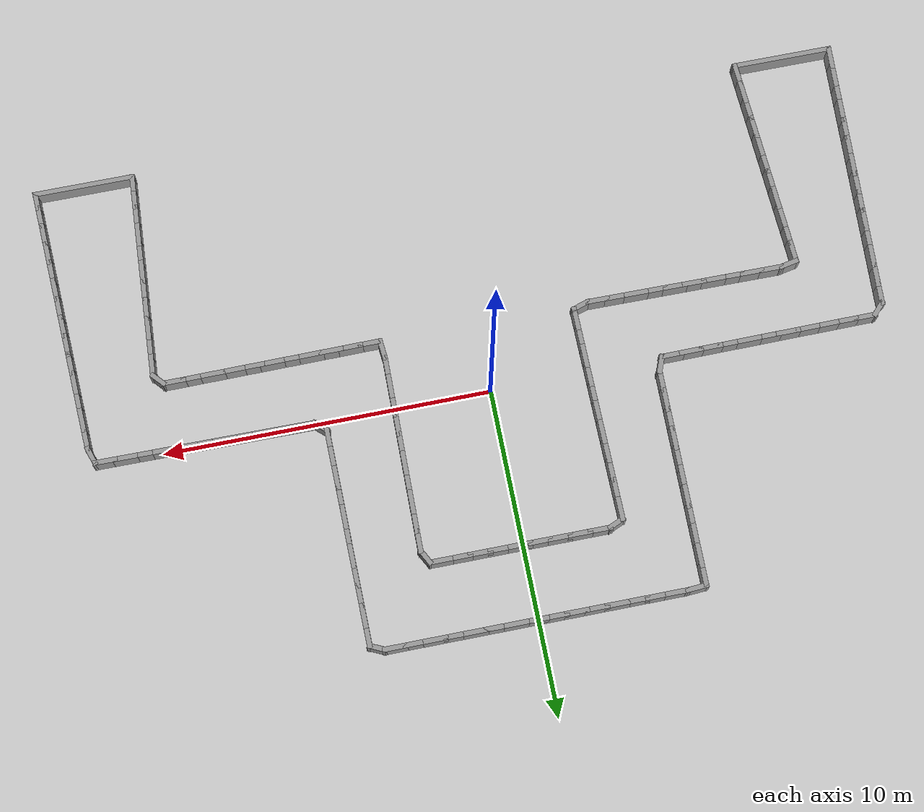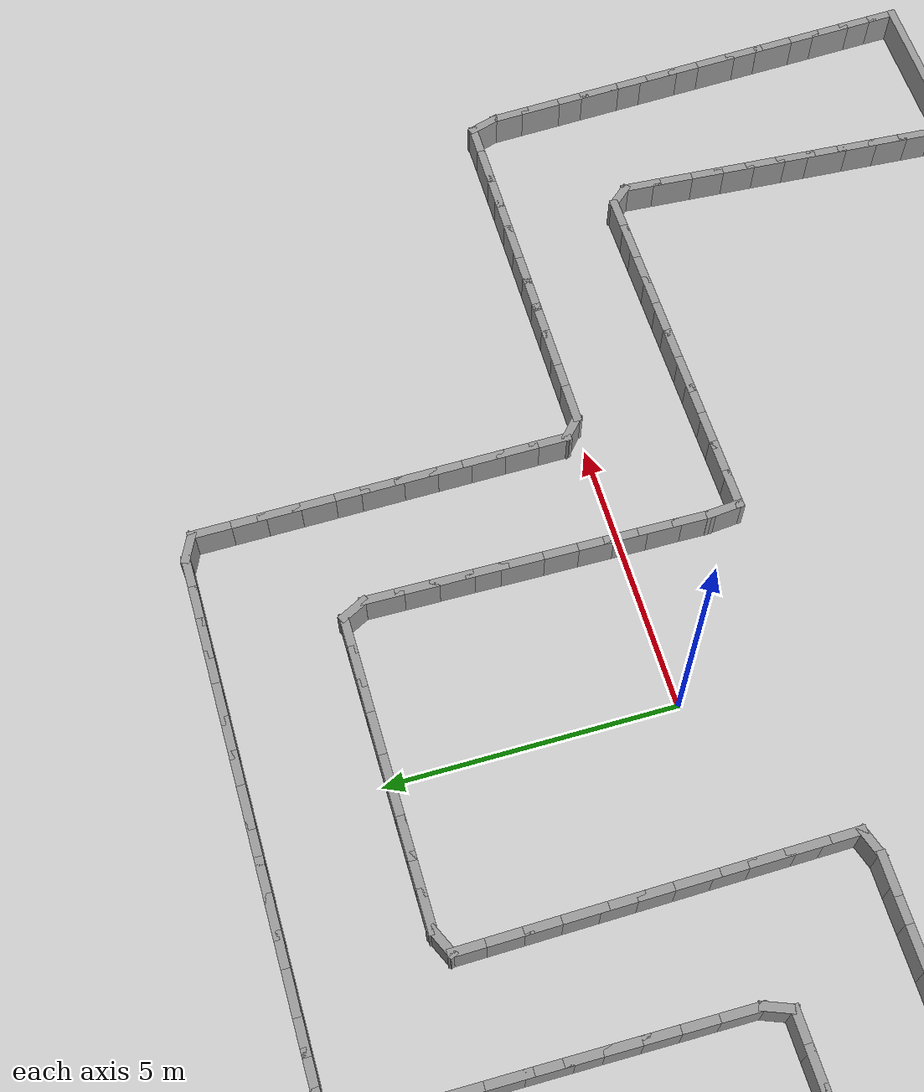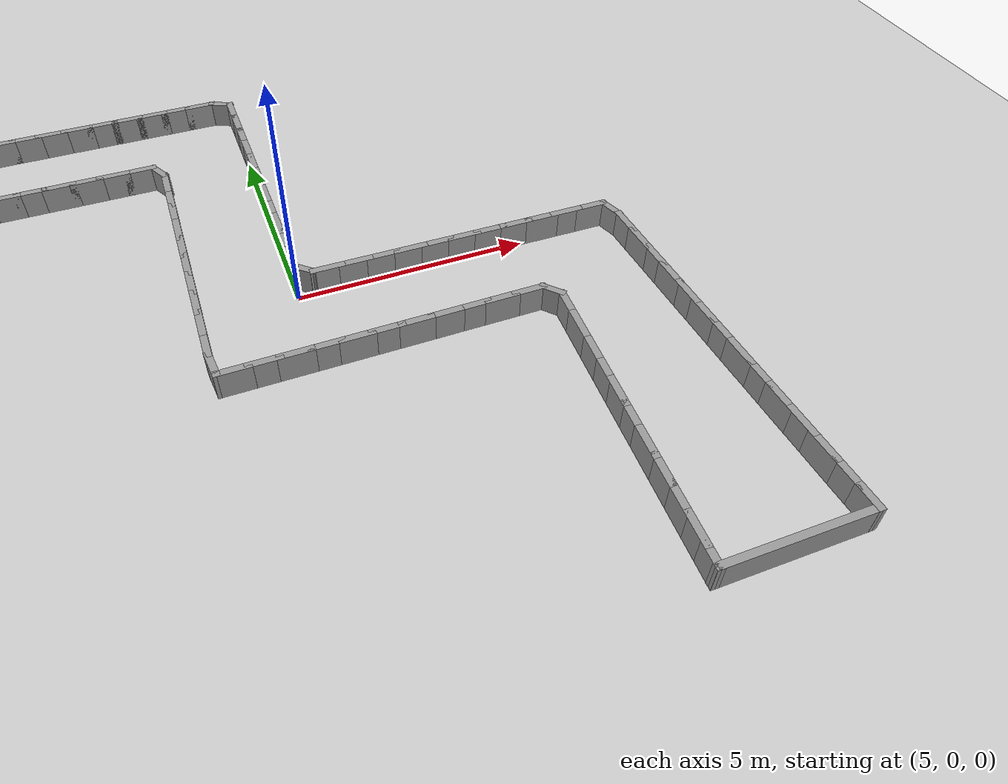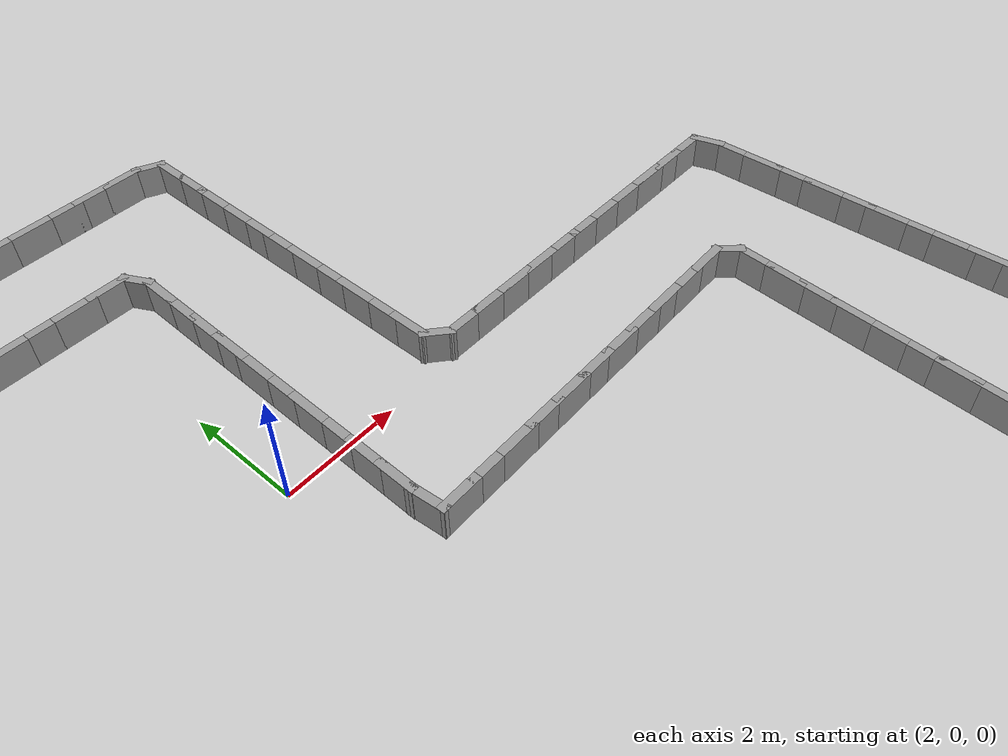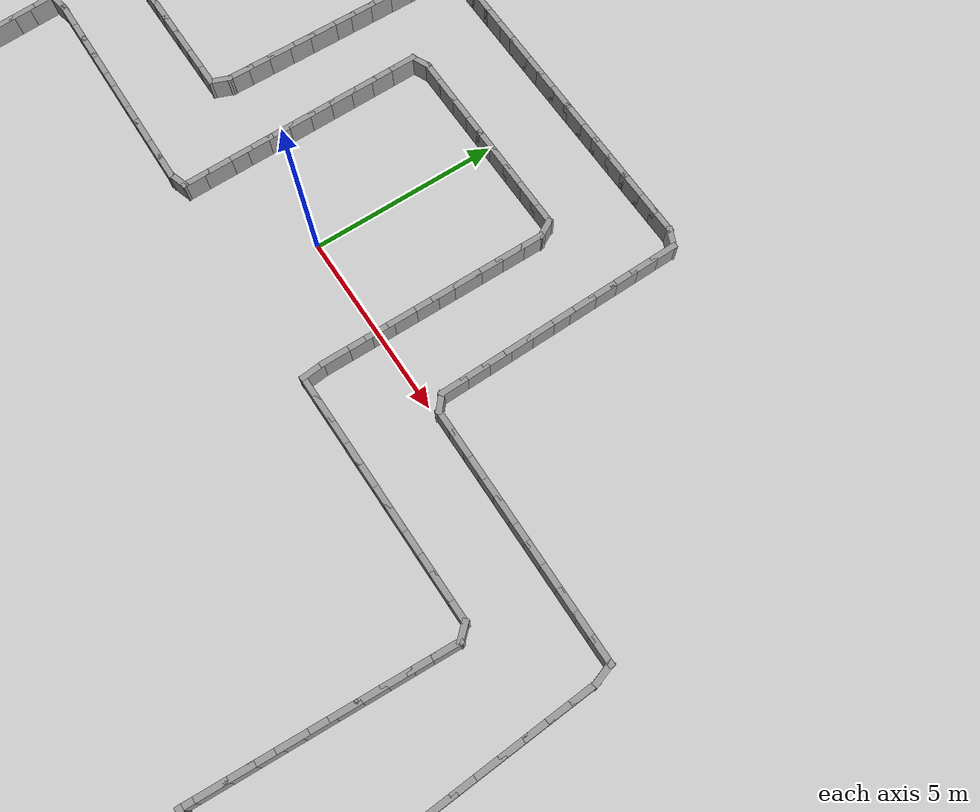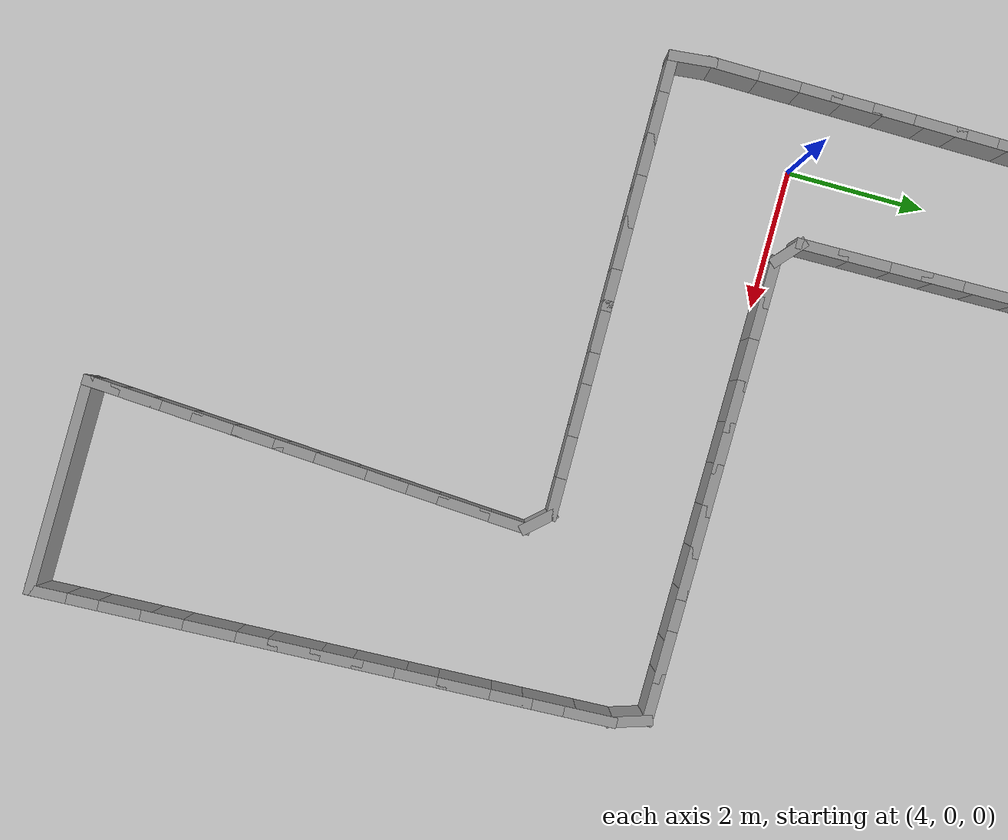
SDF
<?xml version="1.0" ?>
<sdf version='1.7'>
  <world name='default'>
    <plugin name='gazebo_ros_state' filename='libgazebo_ros_state.so'>
      <ros>
        <namespace>/</namespace>
      </ros>
      <update_rate>1000.0</update_rate>
    </plugin>

    <light name='sun' type='directional'>
      <cast_shadows>1</cast_shadows>
      <pose>0 0 10 0 -0 0</pose>
      <diffuse>0.8 0.8 0.8 1</diffuse>
      <specular>0.2 0.2 0.2 1</specular>
      <attenuation>
        <range>1000</range>
        <constant>0.9</constant>
        <linear>0.01</linear>
        <quadratic>0.001</quadratic>
      </attenuation>
      <direction>-0.5 0.1 -0.9</direction>
      <spot>
        <inner_angle>0</inner_angle>
        <outer_angle>0</outer_angle>
        <falloff>0</falloff>
      </spot>
    </light>
    <model name='ground_plane'>
      <static>1</static>
      <link name='link'>
        <collision name='collision'>
          <geometry>
            <plane>
              <normal>0 0 1</normal>
              <size>100 100</size>
            </plane>
          </geometry>
          <surface>
            <friction>
              <ode>
                <mu>100</mu>
                <mu2>50</mu2>
              </ode>
              <torsional>
                <ode/>
              </torsional>
            </friction>
            <contact>
              <ode/>
            </contact>
            <bounce/>
          </surface>
          <max_contacts>10</max_contacts>
        </collision>
        <visual name='visual'>
          <cast_shadows>0</cast_shadows>
          <geometry>
            <plane>
              <normal>0 0 1</normal>
              <size>100 100</size>
            </plane>
          </geometry>
          <material>
            <script>
              <uri>file://media/materials/scripts/gazebo.material</uri>
              <name>Gazebo/Grey</name>
            </script>
          </material>
        </visual>
        <self_collide>0</self_collide>
        <enable_wind>0</enable_wind>
        <kinematic>0</kinematic>
      </link>
    </model>
    <gravity>0 0 -9.8</gravity>
    <magnetic_field>6e-06 2.3e-05 -4.2e-05</magnetic_field>
    <atmosphere type='adiabatic'/>
    <physics type='ode'>
      <max_step_size>0.001</max_step_size>
      <real_time_factor>1</real_time_factor>
      <real_time_update_rate>1000</real_time_update_rate>
    </physics>
    <scene>
      <ambient>0.4 0.4 0.4 1</ambient>
      <background>0.7 0.7 0.7 1</background>
      <shadows>1</shadows>
    </scene>
    <audio>
      <device>default</device>
    </audio>
    <wind/>
    <spherical_coordinates>
      <surface_model>EARTH_WGS84</surface_model>
      <latitude_deg>0</latitude_deg>
      <longitude_deg>0</longitude_deg>
      <elevation>0</elevation>
      <heading_deg>0</heading_deg>
    </spherical_coordinates>
  <model name='maze_corridor_easy'>
    <pose>0 0 0 0 -0 0</pose>
    <link name='Wall_0'>
      <collision name='Wall_0_Collision'>
        <geometry><box><size>0.7500 0.1500 0.6000</size></box></geometry>
        <pose>0 0 0.3000 0 -0 0</pose>
      </collision>
      <visual name='Wall_0_Visual'>
        <pose>0 0 0.3000 0 -0 0</pose>
        <geometry><box><size>0.7500 0.1500 0.6000</size></box></geometry>
        <material>
          <script>
            <uri>file://media/materials/scripts/gazebo.material</uri>
            <name>Gazebo/Grey</name>
          </script>
          <ambient>1 1 1 1</ambient>
        </material>
      </visual>
      <pose>-12.4866 -8.4003 0 0 -0 1.52603</pose>
    </link>
    <link name='Wall_1'>
      <collision name='Wall_1_Collision'>
        <geometry><box><size>0.7500 0.1500 0.6000</size></box></geometry>
        <pose>0 0 0.3000 0 -0 0</pose>
      </collision>
      <visual name='Wall_1_Visual'>
        <pose>0 0 0.3000 0 -0 0</pose>
        <geometry><box><size>0.7500 0.1500 0.6000</size></box></geometry>
        <material>
          <script>
            <uri>file://media/materials/scripts/gazebo.material</uri>
            <name>Gazebo/Grey</name>
          </script>
          <ambient>1 1 1 1</ambient>
        </material>
      </visual>
      <pose>-12.4597 -7.8009 0 0 -0 1.52603</pose>
    </link>
    <link name='Wall_2'>
      <collision name='Wall_2_Collision'>
        <geometry><box><size>0.7500 0.1500 0.6000</size></box></geometry>
        <pose>0 0 0.3000 0 -0 0</pose>
      </collision>
      <visual name='Wall_2_Visual'>
        <pose>0 0 0.3000 0 -0 0</pose>
        <geometry><box><size>0.7500 0.1500 0.6000</size></box></geometry>
        <material>
          <script>
            <uri>file://media/materials/scripts/gazebo.material</uri>
            <name>Gazebo/Grey</name>
          </script>
          <ambient>1 1 1 1</ambient>
        </material>
      </visual>
      <pose>-12.4329 -7.2015 0 0 -0 1.52603</pose>
    </link>
    <link name='Wall_3'>
      <collision name='Wall_3_Collision'>
        <geometry><box><size>0.7500 0.1500 0.6000</size></box></geometry>
        <pose>0 0 0.3000 0 -0 0</pose>
      </collision>
      <visual name='Wall_3_Visual'>
        <pose>0 0 0.3000 0 -0 0</pose>
        <geometry><box><size>0.7500 0.1500 0.6000</size></box></geometry>
        <material>
          <script>
            <uri>file://media/materials/scripts/gazebo.material</uri>
            <name>Gazebo/Grey</name>
          </script>
          <ambient>1 1 1 1</ambient>
        </material>
      </visual>
      <pose>-12.4060 -6.6021 0 0 -0 1.52603</pose>
    </link>
    <link name='Wall_4'>
      <collision name='Wall_4_Collision'>
        <geometry><box><size>0.7500 0.1500 0.6000</size></box></geometry>
        <pose>0 0 0.3000 0 -0 0</pose>
      </collision>
      <visual name='Wall_4_Visual'>
        <pose>0 0 0.3000 0 -0 0</pose>
        <geometry><box><size>0.7500 0.1500 0.6000</size></box></geometry>
        <material>
          <script>
            <uri>file://media/materials/scripts/gazebo.material</uri>
            <name>Gazebo/Grey</name>
          </script>
          <ambient>1 1 1 1</ambient>
        </material>
      </visual>
      <pose>-12.3792 -6.0027 0 0 -0 1.52603</pose>
    </link>
    <link name='Wall_5'>
      <collision name='Wall_5_Collision'>
        <geometry><box><size>0.7500 0.1500 0.6000</size></box></geometry>
        <pose>0 0 0.3000 0 -0 0</pose>
      </collision>
      <visual name='Wall_5_Visual'>
        <pose>0 0 0.3000 0 -0 0</pose>
        <geometry><box><size>0.7500 0.1500 0.6000</size></box></geometry>
        <material>
          <script>
            <uri>file://media/materials/scripts/gazebo.material</uri>
            <name>Gazebo/Grey</name>
          </script>
          <ambient>1 1 1 1</ambient>
        </material>
      </visual>
      <pose>-12.3523 -5.4033 0 0 -0 1.52603</pose>
    </link>
    <link name='Wall_6'>
      <collision name='Wall_6_Collision'>
        <geometry><box><size>0.7500 0.1500 0.6000</size></box></geometry>
        <pose>0 0 0.3000 0 -0 0</pose>
      </collision>
      <visual name='Wall_6_Visual'>
        <pose>0 0 0.3000 0 -0 0</pose>
        <geometry><box><size>0.7500 0.1500 0.6000</size></box></geometry>
        <material>
          <script>
            <uri>file://media/materials/scripts/gazebo.material</uri>
            <name>Gazebo/Grey</name>
          </script>
          <ambient>1 1 1 1</ambient>
        </material>
      </visual>
      <pose>-12.3255 -4.8039 0 0 -0 1.52603</pose>
    </link>
    <link name='Wall_7'>
      <collision name='Wall_7_Collision'>
        <geometry><box><size>0.7500 0.1500 0.6000</size></box></geometry>
        <pose>0 0 0.3000 0 -0 0</pose>
      </collision>
      <visual name='Wall_7_Visual'>
        <pose>0 0 0.3000 0 -0 0</pose>
        <geometry><box><size>0.7500 0.1500 0.6000</size></box></geometry>
        <material>
          <script>
            <uri>file://media/materials/scripts/gazebo.material</uri>
            <name>Gazebo/Grey</name>
          </script>
          <ambient>1 1 1 1</ambient>
        </material>
      </visual>
      <pose>-12.2986 -4.2045 0 0 -0 1.52603</pose>
    </link>
    <link name='Wall_8'>
      <collision name='Wall_8_Collision'>
        <geometry><box><size>0.7500 0.1500 0.6000</size></box></geometry>
        <pose>0 0 0.3000 0 -0 0</pose>
      </collision>
      <visual name='Wall_8_Visual'>
        <pose>0 0 0.3000 0 -0 0</pose>
        <geometry><box><size>0.7500 0.1500 0.6000</size></box></geometry>
        <material>
          <script>
            <uri>file://media/materials/scripts/gazebo.material</uri>
            <name>Gazebo/Grey</name>
          </script>
          <ambient>1 1 1 1</ambient>
        </material>
      </visual>
      <pose>-12.2718 -3.6051 0 0 -0 1.52603</pose>
    </link>
    <link name='Wall_9'>
      <collision name='Wall_9_Collision'>
        <geometry><box><size>0.7500 0.1500 0.6000</size></box></geometry>
        <pose>0 0 0.3000 0 -0 0</pose>
      </collision>
      <visual name='Wall_9_Visual'>
        <pose>0 0 0.3000 0 -0 0</pose>
        <geometry><box><size>0.7500 0.1500 0.6000</size></box></geometry>
        <material>
          <script>
            <uri>file://media/materials/scripts/gazebo.material</uri>
            <name>Gazebo/Grey</name>
          </script>
          <ambient>1 1 1 1</ambient>
        </material>
      </visual>
      <pose>-12.2449 -3.0057 0 0 -0 1.52603</pose>
    </link>
    <link name='Wall_10'>
      <collision name='Wall_10_Collision'>
        <geometry><box><size>0.7500 0.1500 0.6000</size></box></geometry>
        <pose>0 0 0.3000 0 -0 0</pose>
      </collision>
      <visual name='Wall_10_Visual'>
        <pose>0 0 0.3000 0 -0 0</pose>
        <geometry><box><size>0.7500 0.1500 0.6000</size></box></geometry>
        <material>
          <script>
            <uri>file://media/materials/scripts/gazebo.material</uri>
            <name>Gazebo/Grey</name>
          </script>
          <ambient>1 1 1 1</ambient>
        </material>
      </visual>
      <pose>-12.2181 -2.4063 0 0 -0 1.52603</pose>
    </link>
    <link name='Wall_11'>
      <collision name='Wall_11_Collision'>
        <geometry><box><size>0.7500 0.1500 0.6000</size></box></geometry>
        <pose>0 0 0.3000 0 -0 0</pose>
      </collision>
      <visual name='Wall_11_Visual'>
        <pose>0 0 0.3000 0 -0 0</pose>
        <geometry><box><size>0.7500 0.1500 0.6000</size></box></geometry>
        <material>
          <script>
            <uri>file://media/materials/scripts/gazebo.material</uri>
            <name>Gazebo/Grey</name>
          </script>
          <ambient>1 1 1 1</ambient>
        </material>
      </visual>
      <pose>-12.1912 -1.8069 0 0 -0 1.52603</pose>
    </link>
    <link name='Wall_12'>
      <collision name='Wall_12_Collision'>
        <geometry><box><size>0.7500 0.1500 0.6000</size></box></geometry>
        <pose>0 0 0.3000 0 -0 0</pose>
      </collision>
      <visual name='Wall_12_Visual'>
        <pose>0 0 0.3000 0 -0 0</pose>
        <geometry><box><size>0.7500 0.1500 0.6000</size></box></geometry>
        <material>
          <script>
            <uri>file://media/materials/scripts/gazebo.material</uri>
            <name>Gazebo/Grey</name>
          </script>
          <ambient>1 1 1 1</ambient>
        </material>
      </visual>
      <pose>-12.1644 -1.2075 0 0 -0 1.52603</pose>
    </link>
    <link name='Wall_13'>
      <collision name='Wall_13_Collision'>
        <geometry><box><size>0.7500 0.1500 0.6000</size></box></geometry>
        <pose>0 0 0.3000 0 -0 0</pose>
      </collision>
      <visual name='Wall_13_Visual'>
        <pose>0 0 0.3000 0 -0 0</pose>
        <geometry><box><size>0.7500 0.1500 0.6000</size></box></geometry>
        <material>
          <script>
            <uri>file://media/materials/scripts/gazebo.material</uri>
            <name>Gazebo/Grey</name>
          </script>
          <ambient>1 1 1 1</ambient>
        </material>
      </visual>
      <pose>-12.1376 -0.6081 0 0 -0 1.52603</pose>
    </link>
    <link name='Wall_14'>
      <collision name='Wall_14_Collision'>
        <geometry><box><size>0.5859 0.1500 0.6000</size></box></geometry>
        <pose>0 0 0.3000 0 -0 0</pose>
      </collision>
      <visual name='Wall_14_Visual'>
        <pose>0 0 0.3000 0 -0 0</pose>
        <geometry><box><size>0.5859 0.1500 0.6000</size></box></geometry>
        <material>
          <script>
            <uri>file://media/materials/scripts/gazebo.material</uri>
            <name>Gazebo/Grey</name>
          </script>
          <ambient>1 1 1 1</ambient>
        </material>
      </visual>
      <pose>-11.9759 -0.1487 0 0 -0 0.82276</pose>
    </link>
    <link name='Wall_15'>
      <collision name='Wall_15_Collision'>
        <geometry><box><size>0.7500 0.1500 0.6000</size></box></geometry>
        <pose>0 0 0.3000 0 -0 0</pose>
      </collision>
      <visual name='Wall_15_Visual'>
        <pose>0 0 0.3000 0 -0 0</pose>
        <geometry><box><size>0.7500 0.1500 0.6000</size></box></geometry>
        <material>
          <script>
            <uri>file://media/materials/scripts/gazebo.material</uri>
            <name>Gazebo/Grey</name>
          </script>
          <ambient>1 1 1 1</ambient>
        </material>
      </visual>
      <pose>-11.5277 0.0133 0 0 -0 0.00733</pose>
    </link>
    <link name='Wall_16'>
      <collision name='Wall_16_Collision'>
        <geometry><box><size>0.7500 0.1500 0.6000</size></box></geometry>
        <pose>0 0 0.3000 0 -0 0</pose>
      </collision>
      <visual name='Wall_16_Visual'>
        <pose>0 0 0.3000 0 -0 0</pose>
        <geometry><box><size>0.7500 0.1500 0.6000</size></box></geometry>
        <material>
          <script>
            <uri>file://media/materials/scripts/gazebo.material</uri>
            <name>Gazebo/Grey</name>
          </script>
          <ambient>1 1 1 1</ambient>
        </material>
      </visual>
      <pose>-10.9277 0.0177 0 0 -0 0.00733</pose>
    </link>
    <link name='Wall_17'>
      <collision name='Wall_17_Collision'>
        <geometry><box><size>0.7500 0.1500 0.6000</size></box></geometry>
        <pose>0 0 0.3000 0 -0 0</pose>
      </collision>
      <visual name='Wall_17_Visual'>
        <pose>0 0 0.3000 0 -0 0</pose>
        <geometry><box><size>0.7500 0.1500 0.6000</size></box></geometry>
        <material>
          <script>
            <uri>file://media/materials/scripts/gazebo.material</uri>
            <name>Gazebo/Grey</name>
          </script>
          <ambient>1 1 1 1</ambient>
        </material>
      </visual>
      <pose>-10.3277 0.0221 0 0 -0 0.00733</pose>
    </link>
    <link name='Wall_18'>
      <collision name='Wall_18_Collision'>
        <geometry><box><size>0.7500 0.1500 0.6000</size></box></geometry>
        <pose>0 0 0.3000 0 -0 0</pose>
      </collision>
      <visual name='Wall_18_Visual'>
        <pose>0 0 0.3000 0 -0 0</pose>
        <geometry><box><size>0.7500 0.1500 0.6000</size></box></geometry>
        <material>
          <script>
            <uri>file://media/materials/scripts/gazebo.material</uri>
            <name>Gazebo/Grey</name>
          </script>
          <ambient>1 1 1 1</ambient>
        </material>
      </visual>
      <pose>-9.7277 0.0265 0 0 -0 0.00733</pose>
    </link>
    <link name='Wall_19'>
      <collision name='Wall_19_Collision'>
        <geometry><box><size>0.7500 0.1500 0.6000</size></box></geometry>
        <pose>0 0 0.3000 0 -0 0</pose>
      </collision>
      <visual name='Wall_19_Visual'>
        <pose>0 0 0.3000 0 -0 0</pose>
        <geometry><box><size>0.7500 0.1500 0.6000</size></box></geometry>
        <material>
          <script>
            <uri>file://media/materials/scripts/gazebo.material</uri>
            <name>Gazebo/Grey</name>
          </script>
          <ambient>1 1 1 1</ambient>
        </material>
      </visual>
      <pose>-9.1277 0.0309 0 0 -0 0.00733</pose>
    </link>
    <link name='Wall_20'>
      <collision name='Wall_20_Collision'>
        <geometry><box><size>0.7500 0.1500 0.6000</size></box></geometry>
        <pose>0 0 0.3000 0 -0 0</pose>
      </collision>
      <visual name='Wall_20_Visual'>
        <pose>0 0 0.3000 0 -0 0</pose>
        <geometry><box><size>0.7500 0.1500 0.6000</size></box></geometry>
        <material>
          <script>
            <uri>file://media/materials/scripts/gazebo.material</uri>
            <name>Gazebo/Grey</name>
          </script>
          <ambient>1 1 1 1</ambient>
        </material>
      </visual>
      <pose>-8.5277 0.0353 0 0 -0 0.00733</pose>
    </link>
    <link name='Wall_21'>
      <collision name='Wall_21_Collision'>
        <geometry><box><size>0.7500 0.1500 0.6000</size></box></geometry>
        <pose>0 0 0.3000 0 -0 0</pose>
      </collision>
      <visual name='Wall_21_Visual'>
        <pose>0 0 0.3000 0 -0 0</pose>
        <geometry><box><size>0.7500 0.1500 0.6000</size></box></geometry>
        <material>
          <script>
            <uri>file://media/materials/scripts/gazebo.material</uri>
            <name>Gazebo/Grey</name>
          </script>
          <ambient>1 1 1 1</ambient>
        </material>
      </visual>
      <pose>-7.9278 0.0397 0 0 -0 0.00733</pose>
    </link>
    <link name='Wall_22'>
      <collision name='Wall_22_Collision'>
        <geometry><box><size>0.7500 0.1500 0.6000</size></box></geometry>
        <pose>0 0 0.3000 0 -0 0</pose>
      </collision>
      <visual name='Wall_22_Visual'>
        <pose>0 0 0.3000 0 -0 0</pose>
        <geometry><box><size>0.7500 0.1500 0.6000</size></box></geometry>
        <material>
          <script>
            <uri>file://media/materials/scripts/gazebo.material</uri>
            <name>Gazebo/Grey</name>
          </script>
          <ambient>1 1 1 1</ambient>
        </material>
      </visual>
      <pose>-7.3278 0.0440 0 0 -0 0.00733</pose>
    </link>
    <link name='Wall_23'>
      <collision name='Wall_23_Collision'>
        <geometry><box><size>0.7500 0.1500 0.6000</size></box></geometry>
        <pose>0 0 0.3000 0 -0 0</pose>
      </collision>
      <visual name='Wall_23_Visual'>
        <pose>0 0 0.3000 0 -0 0</pose>
        <geometry><box><size>0.7500 0.1500 0.6000</size></box></geometry>
        <material>
          <script>
            <uri>file://media/materials/scripts/gazebo.material</uri>
            <name>Gazebo/Grey</name>
          </script>
          <ambient>1 1 1 1</ambient>
        </material>
      </visual>
      <pose>-6.7278 0.0484 0 0 -0 0.00733</pose>
    </link>
    <link name='Wall_24'>
      <collision name='Wall_24_Collision'>
        <geometry><box><size>0.7500 0.1500 0.6000</size></box></geometry>
        <pose>0 0 0.3000 0 -0 0</pose>
      </collision>
      <visual name='Wall_24_Visual'>
        <pose>0 0 0.3000 0 -0 0</pose>
        <geometry><box><size>0.7500 0.1500 0.6000</size></box></geometry>
        <material>
          <script>
            <uri>file://media/materials/scripts/gazebo.material</uri>
            <name>Gazebo/Grey</name>
          </script>
          <ambient>1 1 1 1</ambient>
        </material>
      </visual>
      <pose>-6.1278 0.0528 0 0 -0 0.00733</pose>
    </link>
    <link name='Wall_25'>
      <collision name='Wall_25_Collision'>
        <geometry><box><size>0.7500 0.1500 0.6000</size></box></geometry>
        <pose>0 0 0.3000 0 -0 0</pose>
      </collision>
      <visual name='Wall_25_Visual'>
        <pose>0 0 0.3000 0 -0 0</pose>
        <geometry><box><size>0.7500 0.1500 0.6000</size></box></geometry>
        <material>
          <script>
            <uri>file://media/materials/scripts/gazebo.material</uri>
            <name>Gazebo/Grey</name>
          </script>
          <ambient>1 1 1 1</ambient>
        </material>
      </visual>
      <pose>-5.5278 0.0572 0 0 -0 0.00733</pose>
    </link>
    <link name='Wall_26'>
      <collision name='Wall_26_Collision'>
        <geometry><box><size>0.6167 0.1500 0.6000</size></box></geometry>
        <pose>0 0 0.3000 0 -0 0</pose>
      </collision>
      <visual name='Wall_26_Visual'>
        <pose>0 0 0.3000 0 -0 0</pose>
        <geometry><box><size>0.6167 0.1500 0.6000</size></box></geometry>
        <material>
          <script>
            <uri>file://media/materials/scripts/gazebo.material</uri>
            <name>Gazebo/Grey</name>
          </script>
          <ambient>1 1 1 1</ambient>
        </material>
      </visual>
      <pose>-5.1420 0.2764 0 0 -0 1.19421</pose>
    </link>
    <link name='Wall_27'>
      <collision name='Wall_27_Collision'>
        <geometry><box><size>0.7500 0.1500 0.6000</size></box></geometry>
        <pose>0 0 0.3000 0 -0 0</pose>
      </collision>
      <visual name='Wall_27_Visual'>
        <pose>0 0 0.3000 0 -0 0</pose>
        <geometry><box><size>0.7500 0.1500 0.6000</size></box></geometry>
        <material>
          <script>
            <uri>file://media/materials/scripts/gazebo.material</uri>
            <name>Gazebo/Grey</name>
          </script>
          <ambient>1 1 1 1</ambient>
        </material>
      </visual>
      <pose>-5.0531 0.7934 0 0 -0 1.56048</pose>
    </link>
    <link name='Wall_28'>
      <collision name='Wall_28_Collision'>
        <geometry><box><size>0.7500 0.1500 0.6000</size></box></geometry>
        <pose>0 0 0.3000 0 -0 0</pose>
      </collision>
      <visual name='Wall_28_Visual'>
        <pose>0 0 0.3000 0 -0 0</pose>
        <geometry><box><size>0.7500 0.1500 0.6000</size></box></geometry>
        <material>
          <script>
            <uri>file://media/materials/scripts/gazebo.material</uri>
            <name>Gazebo/Grey</name>
          </script>
          <ambient>1 1 1 1</ambient>
        </material>
      </visual>
      <pose>-5.0469 1.3934 0 0 -0 1.56048</pose>
    </link>
    <link name='Wall_29'>
      <collision name='Wall_29_Collision'>
        <geometry><box><size>0.7500 0.1500 0.6000</size></box></geometry>
        <pose>0 0 0.3000 0 -0 0</pose>
      </collision>
      <visual name='Wall_29_Visual'>
        <pose>0 0 0.3000 0 -0 0</pose>
        <geometry><box><size>0.7500 0.1500 0.6000</size></box></geometry>
        <material>
          <script>
            <uri>file://media/materials/scripts/gazebo.material</uri>
            <name>Gazebo/Grey</name>
          </script>
          <ambient>1 1 1 1</ambient>
        </material>
      </visual>
      <pose>-5.0407 1.9934 0 0 -0 1.56048</pose>
    </link>
    <link name='Wall_30'>
      <collision name='Wall_30_Collision'>
        <geometry><box><size>0.7500 0.1500 0.6000</size></box></geometry>
        <pose>0 0 0.3000 0 -0 0</pose>
      </collision>
      <visual name='Wall_30_Visual'>
        <pose>0 0 0.3000 0 -0 0</pose>
        <geometry><box><size>0.7500 0.1500 0.6000</size></box></geometry>
        <material>
          <script>
            <uri>file://media/materials/scripts/gazebo.material</uri>
            <name>Gazebo/Grey</name>
          </script>
          <ambient>1 1 1 1</ambient>
        </material>
      </visual>
      <pose>-5.0345 2.5933 0 0 -0 1.56048</pose>
    </link>
    <link name='Wall_31'>
      <collision name='Wall_31_Collision'>
        <geometry><box><size>0.7500 0.1500 0.6000</size></box></geometry>
        <pose>0 0 0.3000 0 -0 0</pose>
      </collision>
      <visual name='Wall_31_Visual'>
        <pose>0 0 0.3000 0 -0 0</pose>
        <geometry><box><size>0.7500 0.1500 0.6000</size></box></geometry>
        <material>
          <script>
            <uri>file://media/materials/scripts/gazebo.material</uri>
            <name>Gazebo/Grey</name>
          </script>
          <ambient>1 1 1 1</ambient>
        </material>
      </visual>
      <pose>-5.0283 3.1933 0 0 -0 1.56048</pose>
    </link>
    <link name='Wall_32'>
      <collision name='Wall_32_Collision'>
        <geometry><box><size>0.7500 0.1500 0.6000</size></box></geometry>
        <pose>0 0 0.3000 0 -0 0</pose>
      </collision>
      <visual name='Wall_32_Visual'>
        <pose>0 0 0.3000 0 -0 0</pose>
        <geometry><box><size>0.7500 0.1500 0.6000</size></box></geometry>
        <material>
          <script>
            <uri>file://media/materials/scripts/gazebo.material</uri>
            <name>Gazebo/Grey</name>
          </script>
          <ambient>1 1 1 1</ambient>
        </material>
      </visual>
      <pose>-5.0222 3.7933 0 0 -0 1.56048</pose>
    </link>
    <link name='Wall_33'>
      <collision name='Wall_33_Collision'>
        <geometry><box><size>0.7500 0.1500 0.6000</size></box></geometry>
        <pose>0 0 0.3000 0 -0 0</pose>
      </collision>
      <visual name='Wall_33_Visual'>
        <pose>0 0 0.3000 0 -0 0</pose>
        <geometry><box><size>0.7500 0.1500 0.6000</size></box></geometry>
        <material>
          <script>
            <uri>file://media/materials/scripts/gazebo.material</uri>
            <name>Gazebo/Grey</name>
          </script>
          <ambient>1 1 1 1</ambient>
        </material>
      </visual>
      <pose>-5.0160 4.3932 0 0 -0 1.56048</pose>
    </link>
    <link name='Wall_34'>
      <collision name='Wall_34_Collision'>
        <geometry><box><size>0.7500 0.1500 0.6000</size></box></geometry>
        <pose>0 0 0.3000 0 -0 0</pose>
      </collision>
      <visual name='Wall_34_Visual'>
        <pose>0 0 0.3000 0 -0 0</pose>
        <geometry><box><size>0.7500 0.1500 0.6000</size></box></geometry>
        <material>
          <script>
            <uri>file://media/materials/scripts/gazebo.material</uri>
            <name>Gazebo/Grey</name>
          </script>
          <ambient>1 1 1 1</ambient>
        </material>
      </visual>
      <pose>-5.0098 4.9932 0 0 -0 1.56048</pose>
    </link>
    <link name='Wall_35'>
      <collision name='Wall_35_Collision'>
        <geometry><box><size>0.7500 0.1500 0.6000</size></box></geometry>
        <pose>0 0 0.3000 0 -0 0</pose>
      </collision>
      <visual name='Wall_35_Visual'>
        <pose>0 0 0.3000 0 -0 0</pose>
        <geometry><box><size>0.7500 0.1500 0.6000</size></box></geometry>
        <material>
          <script>
            <uri>file://media/materials/scripts/gazebo.material</uri>
            <name>Gazebo/Grey</name>
          </script>
          <ambient>1 1 1 1</ambient>
        </material>
      </visual>
      <pose>-5.0036 5.5932 0 0 -0 1.56048</pose>
    </link>
    <link name='Wall_36'>
      <collision name='Wall_36_Collision'>
        <geometry><box><size>0.7500 0.1500 0.6000</size></box></geometry>
        <pose>0 0 0.3000 0 -0 0</pose>
      </collision>
      <visual name='Wall_36_Visual'>
        <pose>0 0 0.3000 0 -0 0</pose>
        <geometry><box><size>0.7500 0.1500 0.6000</size></box></geometry>
        <material>
          <script>
            <uri>file://media/materials/scripts/gazebo.material</uri>
            <name>Gazebo/Grey</name>
          </script>
          <ambient>1 1 1 1</ambient>
        </material>
      </visual>
      <pose>-4.9974 6.1932 0 0 -0 1.56048</pose>
    </link>
    <link name='Wall_37'>
      <collision name='Wall_37_Collision'>
        <geometry><box><size>0.7500 0.1500 0.6000</size></box></geometry>
        <pose>0 0 0.3000 0 -0 0</pose>
      </collision>
      <visual name='Wall_37_Visual'>
        <pose>0 0 0.3000 0 -0 0</pose>
        <geometry><box><size>0.7500 0.1500 0.6000</size></box></geometry>
        <material>
          <script>
            <uri>file://media/materials/scripts/gazebo.material</uri>
            <name>Gazebo/Grey</name>
          </script>
          <ambient>1 1 1 1</ambient>
        </material>
      </visual>
      <pose>-4.9912 6.7931 0 0 -0 1.56048</pose>
    </link>
    <link name='Wall_38'>
      <collision name='Wall_38_Collision'>
        <geometry><box><size>0.7157 0.1500 0.6000</size></box></geometry>
        <pose>0 0 0.3000 0 -0 0</pose>
      </collision>
      <visual name='Wall_38_Visual'>
        <pose>0 0 0.3000 0 -0 0</pose>
        <geometry><box><size>0.7157 0.1500 0.6000</size></box></geometry>
        <material>
          <script>
            <uri>file://media/materials/scripts/gazebo.material</uri>
            <name>Gazebo/Grey</name>
          </script>
          <ambient>1 1 1 1</ambient>
        </material>
      </visual>
      <pose>-4.7058 7.1110 0 0 -0 0.06325</pose>
    </link>
    <link name='Wall_39'>
      <collision name='Wall_39_Collision'>
        <geometry><box><size>0.7500 0.1500 0.6000</size></box></geometry>
        <pose>0 0 0.3000 0 -0 0</pose>
      </collision>
      <visual name='Wall_39_Visual'>
        <pose>0 0 0.3000 0 -0 0</pose>
        <geometry><box><size>0.7500 0.1500 0.6000</size></box></geometry>
        <material>
          <script>
            <uri>file://media/materials/scripts/gazebo.material</uri>
            <name>Gazebo/Grey</name>
          </script>
          <ambient>1 1 1 1</ambient>
        </material>
      </visual>
      <pose>-4.1235 7.1289 0 0 -0 0.00000</pose>
    </link>
    <link name='Wall_40'>
      <collision name='Wall_40_Collision'>
        <geometry><box><size>0.7500 0.1500 0.6000</size></box></geometry>
        <pose>0 0 0.3000 0 -0 0</pose>
      </collision>
      <visual name='Wall_40_Visual'>
        <pose>0 0 0.3000 0 -0 0</pose>
        <geometry><box><size>0.7500 0.1500 0.6000</size></box></geometry>
        <material>
          <script>
            <uri>file://media/materials/scripts/gazebo.material</uri>
            <name>Gazebo/Grey</name>
          </script>
          <ambient>1 1 1 1</ambient>
        </material>
      </visual>
      <pose>-3.5235 7.1289 0 0 -0 0.00000</pose>
    </link>
    <link name='Wall_41'>
      <collision name='Wall_41_Collision'>
        <geometry><box><size>0.7500 0.1500 0.6000</size></box></geometry>
        <pose>0 0 0.3000 0 -0 0</pose>
      </collision>
      <visual name='Wall_41_Visual'>
        <pose>0 0 0.3000 0 -0 0</pose>
        <geometry><box><size>0.7500 0.1500 0.6000</size></box></geometry>
        <material>
          <script>
            <uri>file://media/materials/scripts/gazebo.material</uri>
            <name>Gazebo/Grey</name>
          </script>
          <ambient>1 1 1 1</ambient>
        </material>
      </visual>
      <pose>-2.9235 7.1289 0 0 -0 0.00000</pose>
    </link>
    <link name='Wall_42'>
      <collision name='Wall_42_Collision'>
        <geometry><box><size>0.7500 0.1500 0.6000</size></box></geometry>
        <pose>0 0 0.3000 0 -0 0</pose>
      </collision>
      <visual name='Wall_42_Visual'>
        <pose>0 0 0.3000 0 -0 0</pose>
        <geometry><box><size>0.7500 0.1500 0.6000</size></box></geometry>
        <material>
          <script>
            <uri>file://media/materials/scripts/gazebo.material</uri>
            <name>Gazebo/Grey</name>
          </script>
          <ambient>1 1 1 1</ambient>
        </material>
      </visual>
      <pose>-2.3235 7.1289 0 0 -0 0.00000</pose>
    </link>
    <link name='Wall_43'>
      <collision name='Wall_43_Collision'>
        <geometry><box><size>0.7500 0.1500 0.6000</size></box></geometry>
        <pose>0 0 0.3000 0 -0 0</pose>
      </collision>
      <visual name='Wall_43_Visual'>
        <pose>0 0 0.3000 0 -0 0</pose>
        <geometry><box><size>0.7500 0.1500 0.6000</size></box></geometry>
        <material>
          <script>
            <uri>file://media/materials/scripts/gazebo.material</uri>
            <name>Gazebo/Grey</name>
          </script>
          <ambient>1 1 1 1</ambient>
        </material>
      </visual>
      <pose>-1.7235 7.1289 0 0 -0 0.00000</pose>
    </link>
    <link name='Wall_44'>
      <collision name='Wall_44_Collision'>
        <geometry><box><size>0.7500 0.1500 0.6000</size></box></geometry>
        <pose>0 0 0.3000 0 -0 0</pose>
      </collision>
      <visual name='Wall_44_Visual'>
        <pose>0 0 0.3000 0 -0 0</pose>
        <geometry><box><size>0.7500 0.1500 0.6000</size></box></geometry>
        <material>
          <script>
            <uri>file://media/materials/scripts/gazebo.material</uri>
            <name>Gazebo/Grey</name>
          </script>
          <ambient>1 1 1 1</ambient>
        </material>
      </visual>
      <pose>-1.1235 7.1289 0 0 -0 0.00000</pose>
    </link>
    <link name='Wall_45'>
      <collision name='Wall_45_Collision'>
        <geometry><box><size>0.7500 0.1500 0.6000</size></box></geometry>
        <pose>0 0 0.3000 0 -0 0</pose>
      </collision>
      <visual name='Wall_45_Visual'>
        <pose>0 0 0.3000 0 -0 0</pose>
        <geometry><box><size>0.7500 0.1500 0.6000</size></box></geometry>
        <material>
          <script>
            <uri>file://media/materials/scripts/gazebo.material</uri>
            <name>Gazebo/Grey</name>
          </script>
          <ambient>1 1 1 1</ambient>
        </material>
      </visual>
      <pose>-0.5235 7.1289 0 0 -0 0.00000</pose>
    </link>
    <link name='Wall_46'>
      <collision name='Wall_46_Collision'>
        <geometry><box><size>0.7500 0.1500 0.6000</size></box></geometry>
        <pose>0 0 0.3000 0 -0 0</pose>
      </collision>
      <visual name='Wall_46_Visual'>
        <pose>0 0 0.3000 0 -0 0</pose>
        <geometry><box><size>0.7500 0.1500 0.6000</size></box></geometry>
        <material>
          <script>
            <uri>file://media/materials/scripts/gazebo.material</uri>
            <name>Gazebo/Grey</name>
          </script>
          <ambient>1 1 1 1</ambient>
        </material>
      </visual>
      <pose>0.0765 7.1289 0 0 -0 0.00000</pose>
    </link>
    <link name='Wall_47'>
      <collision name='Wall_47_Collision'>
        <geometry><box><size>0.7500 0.1500 0.6000</size></box></geometry>
        <pose>0 0 0.3000 0 -0 0</pose>
      </collision>
      <visual name='Wall_47_Visual'>
        <pose>0 0 0.3000 0 -0 0</pose>
        <geometry><box><size>0.7500 0.1500 0.6000</size></box></geometry>
        <material>
          <script>
            <uri>file://media/materials/scripts/gazebo.material</uri>
            <name>Gazebo/Grey</name>
          </script>
          <ambient>1 1 1 1</ambient>
        </material>
      </visual>
      <pose>0.6765 7.1289 0 0 -0 0.00000</pose>
    </link>
    <link name='Wall_48'>
      <collision name='Wall_48_Collision'>
        <geometry><box><size>0.7500 0.1500 0.6000</size></box></geometry>
        <pose>0 0 0.3000 0 -0 0</pose>
      </collision>
      <visual name='Wall_48_Visual'>
        <pose>0 0 0.3000 0 -0 0</pose>
        <geometry><box><size>0.7500 0.1500 0.6000</size></box></geometry>
        <material>
          <script>
            <uri>file://media/materials/scripts/gazebo.material</uri>
            <name>Gazebo/Grey</name>
          </script>
          <ambient>1 1 1 1</ambient>
        </material>
      </visual>
      <pose>1.2765 7.1289 0 0 -0 0.00000</pose>
    </link>
    <link name='Wall_49'>
      <collision name='Wall_49_Collision'>
        <geometry><box><size>0.7500 0.1500 0.6000</size></box></geometry>
        <pose>0 0 0.3000 0 -0 0</pose>
      </collision>
      <visual name='Wall_49_Visual'>
        <pose>0 0 0.3000 0 -0 0</pose>
        <geometry><box><size>0.7500 0.1500 0.6000</size></box></geometry>
        <material>
          <script>
            <uri>file://media/materials/scripts/gazebo.material</uri>
            <name>Gazebo/Grey</name>
          </script>
          <ambient>1 1 1 1</ambient>
        </material>
      </visual>
      <pose>1.8765 7.1289 0 0 -0 0.00000</pose>
    </link>
    <link name='Wall_50'>
      <collision name='Wall_50_Collision'>
        <geometry><box><size>0.7500 0.1500 0.6000</size></box></geometry>
        <pose>0 0 0.3000 0 -0 0</pose>
      </collision>
      <visual name='Wall_50_Visual'>
        <pose>0 0 0.3000 0 -0 0</pose>
        <geometry><box><size>0.7500 0.1500 0.6000</size></box></geometry>
        <material>
          <script>
            <uri>file://media/materials/scripts/gazebo.material</uri>
            <name>Gazebo/Grey</name>
          </script>
          <ambient>1 1 1 1</ambient>
        </material>
      </visual>
      <pose>2.4765 7.1289 0 0 -0 0.00000</pose>
    </link>
    <link name='Wall_51'>
      <collision name='Wall_51_Collision'>
        <geometry><box><size>0.7500 0.1500 0.6000</size></box></geometry>
        <pose>0 0 0.3000 0 -0 0</pose>
      </collision>
      <visual name='Wall_51_Visual'>
        <pose>0 0 0.3000 0 -0 0</pose>
        <geometry><box><size>0.7500 0.1500 0.6000</size></box></geometry>
        <material>
          <script>
            <uri>file://media/materials/scripts/gazebo.material</uri>
            <name>Gazebo/Grey</name>
          </script>
          <ambient>1 1 1 1</ambient>
        </material>
      </visual>
      <pose>3.0765 7.1289 0 0 -0 0.00000</pose>
    </link>
    <link name='Wall_52'>
      <collision name='Wall_52_Collision'>
        <geometry><box><size>0.7500 0.1500 0.6000</size></box></geometry>
        <pose>0 0 0.3000 0 -0 0</pose>
      </collision>
      <visual name='Wall_52_Visual'>
        <pose>0 0 0.3000 0 -0 0</pose>
        <geometry><box><size>0.7500 0.1500 0.6000</size></box></geometry>
        <material>
          <script>
            <uri>file://media/materials/scripts/gazebo.material</uri>
            <name>Gazebo/Grey</name>
          </script>
          <ambient>1 1 1 1</ambient>
        </material>
      </visual>
      <pose>3.6765 7.1289 0 0 -0 0.00000</pose>
    </link>
    <link name='Wall_53'>
      <collision name='Wall_53_Collision'>
        <geometry><box><size>0.7500 0.1500 0.6000</size></box></geometry>
        <pose>0 0 0.3000 0 -0 0</pose>
      </collision>
      <visual name='Wall_53_Visual'>
        <pose>0 0 0.3000 0 -0 0</pose>
        <geometry><box><size>0.7500 0.1500 0.6000</size></box></geometry>
        <material>
          <script>
            <uri>file://media/materials/scripts/gazebo.material</uri>
            <name>Gazebo/Grey</name>
          </script>
          <ambient>1 1 1 1</ambient>
        </material>
      </visual>
      <pose>4.2765 7.1289 0 0 -0 0.00000</pose>
    </link>
    <link name='Wall_54'>
      <collision name='Wall_54_Collision'>
        <geometry><box><size>0.6043 0.1500 0.6000</size></box></geometry>
        <pose>0 0 0.3000 0 -0 0</pose>
      </collision>
      <visual name='Wall_54_Visual'>
        <pose>0 0 0.3000 0 -0 0</pose>
        <geometry><box><size>0.6043 0.1500 0.6000</size></box></geometry>
        <material>
          <script>
            <uri>file://media/materials/scripts/gazebo.material</uri>
            <name>Gazebo/Grey</name>
          </script>
          <ambient>1 1 1 1</ambient>
        </material>
      </visual>
      <pose>4.7831 7.0345 0 0 -0 -0.42841</pose>
    </link>
    <link name='Wall_55'>
      <collision name='Wall_55_Collision'>
        <geometry><box><size>0.7500 0.1500 0.6000</size></box></geometry>
        <pose>0 0 0.3000 0 -0 0</pose>
      </collision>
      <visual name='Wall_55_Visual'>
        <pose>0 0 0.3000 0 -0 0</pose>
        <geometry><box><size>0.7500 0.1500 0.6000</size></box></geometry>
        <material>
          <script>
            <uri>file://media/materials/scripts/gazebo.material</uri>
            <name>Gazebo/Grey</name>
          </script>
          <ambient>1 1 1 1</ambient>
        </material>
      </visual>
      <pose>4.9928 6.6402 0 0 -0 -1.56048</pose>
    </link>
    <link name='Wall_56'>
      <collision name='Wall_56_Collision'>
        <geometry><box><size>0.7500 0.1500 0.6000</size></box></geometry>
        <pose>0 0 0.3000 0 -0 0</pose>
      </collision>
      <visual name='Wall_56_Visual'>
        <pose>0 0 0.3000 0 -0 0</pose>
        <geometry><box><size>0.7500 0.1500 0.6000</size></box></geometry>
        <material>
          <script>
            <uri>file://media/materials/scripts/gazebo.material</uri>
            <name>Gazebo/Grey</name>
          </script>
          <ambient>1 1 1 1</ambient>
        </material>
      </visual>
      <pose>4.9990 6.0402 0 0 -0 -1.56048</pose>
    </link>
    <link name='Wall_57'>
      <collision name='Wall_57_Collision'>
        <geometry><box><size>0.7500 0.1500 0.6000</size></box></geometry>
        <pose>0 0 0.3000 0 -0 0</pose>
      </collision>
      <visual name='Wall_57_Visual'>
        <pose>0 0 0.3000 0 -0 0</pose>
        <geometry><box><size>0.7500 0.1500 0.6000</size></box></geometry>
        <material>
          <script>
            <uri>file://media/materials/scripts/gazebo.material</uri>
            <name>Gazebo/Grey</name>
          </script>
          <ambient>1 1 1 1</ambient>
        </material>
      </visual>
      <pose>5.0052 5.4402 0 0 -0 -1.56048</pose>
    </link>
    <link name='Wall_58'>
      <collision name='Wall_58_Collision'>
        <geometry><box><size>0.7500 0.1500 0.6000</size></box></geometry>
        <pose>0 0 0.3000 0 -0 0</pose>
      </collision>
      <visual name='Wall_58_Visual'>
        <pose>0 0 0.3000 0 -0 0</pose>
        <geometry><box><size>0.7500 0.1500 0.6000</size></box></geometry>
        <material>
          <script>
            <uri>file://media/materials/scripts/gazebo.material</uri>
            <name>Gazebo/Grey</name>
          </script>
          <ambient>1 1 1 1</ambient>
        </material>
      </visual>
      <pose>5.0114 4.8403 0 0 -0 -1.56048</pose>
    </link>
    <link name='Wall_59'>
      <collision name='Wall_59_Collision'>
        <geometry><box><size>0.7500 0.1500 0.6000</size></box></geometry>
        <pose>0 0 0.3000 0 -0 0</pose>
      </collision>
      <visual name='Wall_59_Visual'>
        <pose>0 0 0.3000 0 -0 0</pose>
        <geometry><box><size>0.7500 0.1500 0.6000</size></box></geometry>
        <material>
          <script>
            <uri>file://media/materials/scripts/gazebo.material</uri>
            <name>Gazebo/Grey</name>
          </script>
          <ambient>1 1 1 1</ambient>
        </material>
      </visual>
      <pose>5.0176 4.2403 0 0 -0 -1.56048</pose>
    </link>
    <link name='Wall_60'>
      <collision name='Wall_60_Collision'>
        <geometry><box><size>0.7500 0.1500 0.6000</size></box></geometry>
        <pose>0 0 0.3000 0 -0 0</pose>
      </collision>
      <visual name='Wall_60_Visual'>
        <pose>0 0 0.3000 0 -0 0</pose>
        <geometry><box><size>0.7500 0.1500 0.6000</size></box></geometry>
        <material>
          <script>
            <uri>file://media/materials/scripts/gazebo.material</uri>
            <name>Gazebo/Grey</name>
          </script>
          <ambient>1 1 1 1</ambient>
        </material>
      </visual>
      <pose>5.0237 3.6403 0 0 -0 -1.56048</pose>
    </link>
    <link name='Wall_61'>
      <collision name='Wall_61_Collision'>
        <geometry><box><size>0.7500 0.1500 0.6000</size></box></geometry>
        <pose>0 0 0.3000 0 -0 0</pose>
      </collision>
      <visual name='Wall_61_Visual'>
        <pose>0 0 0.3000 0 -0 0</pose>
        <geometry><box><size>0.7500 0.1500 0.6000</size></box></geometry>
        <material>
          <script>
            <uri>file://media/materials/scripts/gazebo.material</uri>
            <name>Gazebo/Grey</name>
          </script>
          <ambient>1 1 1 1</ambient>
        </material>
      </visual>
      <pose>5.0299 3.0404 0 0 -0 -1.56048</pose>
    </link>
    <link name='Wall_62'>
      <collision name='Wall_62_Collision'>
        <geometry><box><size>0.7500 0.1500 0.6000</size></box></geometry>
        <pose>0 0 0.3000 0 -0 0</pose>
      </collision>
      <visual name='Wall_62_Visual'>
        <pose>0 0 0.3000 0 -0 0</pose>
        <geometry><box><size>0.7500 0.1500 0.6000</size></box></geometry>
        <material>
          <script>
            <uri>file://media/materials/scripts/gazebo.material</uri>
            <name>Gazebo/Grey</name>
          </script>
          <ambient>1 1 1 1</ambient>
        </material>
      </visual>
      <pose>5.0361 2.4404 0 0 -0 -1.56048</pose>
    </link>
    <link name='Wall_63'>
      <collision name='Wall_63_Collision'>
        <geometry><box><size>0.7500 0.1500 0.6000</size></box></geometry>
        <pose>0 0 0.3000 0 -0 0</pose>
      </collision>
      <visual name='Wall_63_Visual'>
        <pose>0 0 0.3000 0 -0 0</pose>
        <geometry><box><size>0.7500 0.1500 0.6000</size></box></geometry>
        <material>
          <script>
            <uri>file://media/materials/scripts/gazebo.material</uri>
            <name>Gazebo/Grey</name>
          </script>
          <ambient>1 1 1 1</ambient>
        </material>
      </visual>
      <pose>5.0423 1.8404 0 0 -0 -1.56048</pose>
    </link>
    <link name='Wall_64'>
      <collision name='Wall_64_Collision'>
        <geometry><box><size>0.7500 0.1500 0.6000</size></box></geometry>
        <pose>0 0 0.3000 0 -0 0</pose>
      </collision>
      <visual name='Wall_64_Visual'>
        <pose>0 0 0.3000 0 -0 0</pose>
        <geometry><box><size>0.7500 0.1500 0.6000</size></box></geometry>
        <material>
          <script>
            <uri>file://media/materials/scripts/gazebo.material</uri>
            <name>Gazebo/Grey</name>
          </script>
          <ambient>1 1 1 1</ambient>
        </material>
      </visual>
      <pose>5.0485 1.2405 0 0 -0 -1.56048</pose>
    </link>
    <link name='Wall_65'>
      <collision name='Wall_65_Collision'>
        <geometry><box><size>0.7500 0.1500 0.6000</size></box></geometry>
        <pose>0 0 0.3000 0 -0 0</pose>
      </collision>
      <visual name='Wall_65_Visual'>
        <pose>0 0 0.3000 0 -0 0</pose>
        <geometry><box><size>0.7500 0.1500 0.6000</size></box></geometry>
        <material>
          <script>
            <uri>file://media/materials/scripts/gazebo.material</uri>
            <name>Gazebo/Grey</name>
          </script>
          <ambient>1 1 1 1</ambient>
        </material>
      </visual>
      <pose>5.0547 0.6405 0 0 -0 -1.56048</pose>
    </link>
    <link name='Wall_66'>
      <collision name='Wall_66_Collision'>
        <geometry><box><size>0.5789 0.1500 0.6000</size></box></geometry>
        <pose>0 0 0.3000 0 -0 0</pose>
      </collision>
      <visual name='Wall_66_Visual'>
        <pose>0 0 0.3000 0 -0 0</pose>
        <geometry><box><size>0.5789 0.1500 0.6000</size></box></geometry>
        <material>
          <script>
            <uri>file://media/materials/scripts/gazebo.material</uri>
            <name>Gazebo/Grey</name>
          </script>
          <ambient>1 1 1 1</ambient>
        </material>
      </visual>
      <pose>5.2193 0.1994 0 0 -0 -0.71803</pose>
    </link>
    <link name='Wall_67'>
      <collision name='Wall_67_Collision'>
        <geometry><box><size>0.7500 0.1500 0.6000</size></box></geometry>
        <pose>0 0 0.3000 0 -0 0</pose>
      </collision>
      <visual name='Wall_67_Visual'>
        <pose>0 0 0.3000 0 -0 0</pose>
        <geometry><box><size>0.7500 0.1500 0.6000</size></box></geometry>
        <material>
          <script>
            <uri>file://media/materials/scripts/gazebo.material</uri>
            <name>Gazebo/Grey</name>
          </script>
          <ambient>1 1 1 1</ambient>
        </material>
      </visual>
      <pose>5.6808 0.0561 0 0 -0 -0.00733</pose>
    </link>
    <link name='Wall_68'>
      <collision name='Wall_68_Collision'>
        <geometry><box><size>0.7500 0.1500 0.6000</size></box></geometry>
        <pose>0 0 0.3000 0 -0 0</pose>
      </collision>
      <visual name='Wall_68_Visual'>
        <pose>0 0 0.3000 0 -0 0</pose>
        <geometry><box><size>0.7500 0.1500 0.6000</size></box></geometry>
        <material>
          <script>
            <uri>file://media/materials/scripts/gazebo.material</uri>
            <name>Gazebo/Grey</name>
          </script>
          <ambient>1 1 1 1</ambient>
        </material>
      </visual>
      <pose>6.2808 0.0517 0 0 -0 -0.00733</pose>
    </link>
    <link name='Wall_69'>
      <collision name='Wall_69_Collision'>
        <geometry><box><size>0.7500 0.1500 0.6000</size></box></geometry>
        <pose>0 0 0.3000 0 -0 0</pose>
      </collision>
      <visual name='Wall_69_Visual'>
        <pose>0 0 0.3000 0 -0 0</pose>
        <geometry><box><size>0.7500 0.1500 0.6000</size></box></geometry>
        <material>
          <script>
            <uri>file://media/materials/scripts/gazebo.material</uri>
            <name>Gazebo/Grey</name>
          </script>
          <ambient>1 1 1 1</ambient>
        </material>
      </visual>
      <pose>6.8808 0.0473 0 0 -0 -0.00733</pose>
    </link>
    <link name='Wall_70'>
      <collision name='Wall_70_Collision'>
        <geometry><box><size>0.7500 0.1500 0.6000</size></box></geometry>
        <pose>0 0 0.3000 0 -0 0</pose>
      </collision>
      <visual name='Wall_70_Visual'>
        <pose>0 0 0.3000 0 -0 0</pose>
        <geometry><box><size>0.7500 0.1500 0.6000</size></box></geometry>
        <material>
          <script>
            <uri>file://media/materials/scripts/gazebo.material</uri>
            <name>Gazebo/Grey</name>
          </script>
          <ambient>1 1 1 1</ambient>
        </material>
      </visual>
      <pose>7.4807 0.0429 0 0 -0 -0.00733</pose>
    </link>
    <link name='Wall_71'>
      <collision name='Wall_71_Collision'>
        <geometry><box><size>0.7500 0.1500 0.6000</size></box></geometry>
        <pose>0 0 0.3000 0 -0 0</pose>
      </collision>
      <visual name='Wall_71_Visual'>
        <pose>0 0 0.3000 0 -0 0</pose>
        <geometry><box><size>0.7500 0.1500 0.6000</size></box></geometry>
        <material>
          <script>
            <uri>file://media/materials/scripts/gazebo.material</uri>
            <name>Gazebo/Grey</name>
          </script>
          <ambient>1 1 1 1</ambient>
        </material>
      </visual>
      <pose>8.0807 0.0385 0 0 -0 -0.00733</pose>
    </link>
    <link name='Wall_72'>
      <collision name='Wall_72_Collision'>
        <geometry><box><size>0.7500 0.1500 0.6000</size></box></geometry>
        <pose>0 0 0.3000 0 -0 0</pose>
      </collision>
      <visual name='Wall_72_Visual'>
        <pose>0 0 0.3000 0 -0 0</pose>
        <geometry><box><size>0.7500 0.1500 0.6000</size></box></geometry>
        <material>
          <script>
            <uri>file://media/materials/scripts/gazebo.material</uri>
            <name>Gazebo/Grey</name>
          </script>
          <ambient>1 1 1 1</ambient>
        </material>
      </visual>
      <pose>8.6807 0.0341 0 0 -0 -0.00733</pose>
    </link>
    <link name='Wall_73'>
      <collision name='Wall_73_Collision'>
        <geometry><box><size>0.7500 0.1500 0.6000</size></box></geometry>
        <pose>0 0 0.3000 0 -0 0</pose>
      </collision>
      <visual name='Wall_73_Visual'>
        <pose>0 0 0.3000 0 -0 0</pose>
        <geometry><box><size>0.7500 0.1500 0.6000</size></box></geometry>
        <material>
          <script>
            <uri>file://media/materials/scripts/gazebo.material</uri>
            <name>Gazebo/Grey</name>
          </script>
          <ambient>1 1 1 1</ambient>
        </material>
      </visual>
      <pose>9.2807 0.0297 0 0 -0 -0.00733</pose>
    </link>
    <link name='Wall_74'>
      <collision name='Wall_74_Collision'>
        <geometry><box><size>0.7500 0.1500 0.6000</size></box></geometry>
        <pose>0 0 0.3000 0 -0 0</pose>
      </collision>
      <visual name='Wall_74_Visual'>
        <pose>0 0 0.3000 0 -0 0</pose>
        <geometry><box><size>0.7500 0.1500 0.6000</size></box></geometry>
        <material>
          <script>
            <uri>file://media/materials/scripts/gazebo.material</uri>
            <name>Gazebo/Grey</name>
          </script>
          <ambient>1 1 1 1</ambient>
        </material>
      </visual>
      <pose>9.8807 0.0253 0 0 -0 -0.00733</pose>
    </link>
    <link name='Wall_75'>
      <collision name='Wall_75_Collision'>
        <geometry><box><size>0.7500 0.1500 0.6000</size></box></geometry>
        <pose>0 0 0.3000 0 -0 0</pose>
      </collision>
      <visual name='Wall_75_Visual'>
        <pose>0 0 0.3000 0 -0 0</pose>
        <geometry><box><size>0.7500 0.1500 0.6000</size></box></geometry>
        <material>
          <script>
            <uri>file://media/materials/scripts/gazebo.material</uri>
            <name>Gazebo/Grey</name>
          </script>
          <ambient>1 1 1 1</ambient>
        </material>
      </visual>
      <pose>10.4807 0.0209 0 0 -0 -0.00733</pose>
    </link>
    <link name='Wall_76'>
      <collision name='Wall_76_Collision'>
        <geometry><box><size>0.7500 0.1500 0.6000</size></box></geometry>
        <pose>0 0 0.3000 0 -0 0</pose>
      </collision>
      <visual name='Wall_76_Visual'>
        <pose>0 0 0.3000 0 -0 0</pose>
        <geometry><box><size>0.7500 0.1500 0.6000</size></box></geometry>
        <material>
          <script>
            <uri>file://media/materials/scripts/gazebo.material</uri>
            <name>Gazebo/Grey</name>
          </script>
          <ambient>1 1 1 1</ambient>
        </material>
      </visual>
      <pose>11.0806 0.0166 0 0 -0 -0.00733</pose>
    </link>
    <link name='Wall_77'>
      <collision name='Wall_77_Collision'>
        <geometry><box><size>0.7500 0.1500 0.6000</size></box></geometry>
        <pose>0 0 0.3000 0 -0 0</pose>
      </collision>
      <visual name='Wall_77_Visual'>
        <pose>0 0 0.3000 0 -0 0</pose>
        <geometry><box><size>0.7500 0.1500 0.6000</size></box></geometry>
        <material>
          <script>
            <uri>file://media/materials/scripts/gazebo.material</uri>
            <name>Gazebo/Grey</name>
          </script>
          <ambient>1 1 1 1</ambient>
        </material>
      </visual>
      <pose>11.6806 0.0122 0 0 -0 -0.00733</pose>
    </link>
    <link name='Wall_78'>
      <collision name='Wall_78_Collision'>
        <geometry><box><size>0.6446 0.1500 0.6000</size></box></geometry>
        <pose>0 0 0.3000 0 -0 0</pose>
      </collision>
      <visual name='Wall_78_Visual'>
        <pose>0 0 0.3000 0 -0 0</pose>
        <geometry><box><size>0.6446 0.1500 0.6000</size></box></geometry>
        <material>
          <script>
            <uri>file://media/materials/scripts/gazebo.material</uri>
            <name>Gazebo/Grey</name>
          </script>
          <ambient>1 1 1 1</ambient>
        </material>
      </visual>
      <pose>12.0558 -0.2256 0 0 -0 -1.26191</pose>
    </link>
    <link name='Wall_79'>
      <collision name='Wall_79_Collision'>
        <geometry><box><size>0.7500 0.1500 0.6000</size></box></geometry>
        <pose>0 0 0.3000 0 -0 0</pose>
      </collision>
      <visual name='Wall_79_Visual'>
        <pose>0 0 0.3000 0 -0 0</pose>
        <geometry><box><size>0.7500 0.1500 0.6000</size></box></geometry>
        <material>
          <script>
            <uri>file://media/materials/scripts/gazebo.material</uri>
            <name>Gazebo/Grey</name>
          </script>
          <ambient>1 1 1 1</ambient>
        </material>
      </visual>
      <pose>12.1444 -0.7609 0 0 -0 -1.52603</pose>
    </link>
    <link name='Wall_80'>
      <collision name='Wall_80_Collision'>
        <geometry><box><size>0.7500 0.1500 0.6000</size></box></geometry>
        <pose>0 0 0.3000 0 -0 0</pose>
      </collision>
      <visual name='Wall_80_Visual'>
        <pose>0 0 0.3000 0 -0 0</pose>
        <geometry><box><size>0.7500 0.1500 0.6000</size></box></geometry>
        <material>
          <script>
            <uri>file://media/materials/scripts/gazebo.material</uri>
            <name>Gazebo/Grey</name>
          </script>
          <ambient>1 1 1 1</ambient>
        </material>
      </visual>
      <pose>12.1712 -1.3603 0 0 -0 -1.52603</pose>
    </link>
    <link name='Wall_81'>
      <collision name='Wall_81_Collision'>
        <geometry><box><size>0.7500 0.1500 0.6000</size></box></geometry>
        <pose>0 0 0.3000 0 -0 0</pose>
      </collision>
      <visual name='Wall_81_Visual'>
        <pose>0 0 0.3000 0 -0 0</pose>
        <geometry><box><size>0.7500 0.1500 0.6000</size></box></geometry>
        <material>
          <script>
            <uri>file://media/materials/scripts/gazebo.material</uri>
            <name>Gazebo/Grey</name>
          </script>
          <ambient>1 1 1 1</ambient>
        </material>
      </visual>
      <pose>12.1981 -1.9597 0 0 -0 -1.52603</pose>
    </link>
    <link name='Wall_82'>
      <collision name='Wall_82_Collision'>
        <geometry><box><size>0.7500 0.1500 0.6000</size></box></geometry>
        <pose>0 0 0.3000 0 -0 0</pose>
      </collision>
      <visual name='Wall_82_Visual'>
        <pose>0 0 0.3000 0 -0 0</pose>
        <geometry><box><size>0.7500 0.1500 0.6000</size></box></geometry>
        <material>
          <script>
            <uri>file://media/materials/scripts/gazebo.material</uri>
            <name>Gazebo/Grey</name>
          </script>
          <ambient>1 1 1 1</ambient>
        </material>
      </visual>
      <pose>12.2249 -2.5591 0 0 -0 -1.52603</pose>
    </link>
    <link name='Wall_83'>
      <collision name='Wall_83_Collision'>
        <geometry><box><size>0.7500 0.1500 0.6000</size></box></geometry>
        <pose>0 0 0.3000 0 -0 0</pose>
      </collision>
      <visual name='Wall_83_Visual'>
        <pose>0 0 0.3000 0 -0 0</pose>
        <geometry><box><size>0.7500 0.1500 0.6000</size></box></geometry>
        <material>
          <script>
            <uri>file://media/materials/scripts/gazebo.material</uri>
            <name>Gazebo/Grey</name>
          </script>
          <ambient>1 1 1 1</ambient>
        </material>
      </visual>
      <pose>12.2518 -3.1585 0 0 -0 -1.52603</pose>
    </link>
    <link name='Wall_84'>
      <collision name='Wall_84_Collision'>
        <geometry><box><size>0.7500 0.1500 0.6000</size></box></geometry>
        <pose>0 0 0.3000 0 -0 0</pose>
      </collision>
      <visual name='Wall_84_Visual'>
        <pose>0 0 0.3000 0 -0 0</pose>
        <geometry><box><size>0.7500 0.1500 0.6000</size></box></geometry>
        <material>
          <script>
            <uri>file://media/materials/scripts/gazebo.material</uri>
            <name>Gazebo/Grey</name>
          </script>
          <ambient>1 1 1 1</ambient>
        </material>
      </visual>
      <pose>12.2786 -3.7579 0 0 -0 -1.52603</pose>
    </link>
    <link name='Wall_85'>
      <collision name='Wall_85_Collision'>
        <geometry><box><size>0.7500 0.1500 0.6000</size></box></geometry>
        <pose>0 0 0.3000 0 -0 0</pose>
      </collision>
      <visual name='Wall_85_Visual'>
        <pose>0 0 0.3000 0 -0 0</pose>
        <geometry><box><size>0.7500 0.1500 0.6000</size></box></geometry>
        <material>
          <script>
            <uri>file://media/materials/scripts/gazebo.material</uri>
            <name>Gazebo/Grey</name>
          </script>
          <ambient>1 1 1 1</ambient>
        </material>
      </visual>
      <pose>12.3055 -4.3573 0 0 -0 -1.52603</pose>
    </link>
    <link name='Wall_86'>
      <collision name='Wall_86_Collision'>
        <geometry><box><size>0.7500 0.1500 0.6000</size></box></geometry>
        <pose>0 0 0.3000 0 -0 0</pose>
      </collision>
      <visual name='Wall_86_Visual'>
        <pose>0 0 0.3000 0 -0 0</pose>
        <geometry><box><size>0.7500 0.1500 0.6000</size></box></geometry>
        <material>
          <script>
            <uri>file://media/materials/scripts/gazebo.material</uri>
            <name>Gazebo/Grey</name>
          </script>
          <ambient>1 1 1 1</ambient>
        </material>
      </visual>
      <pose>12.3323 -4.9567 0 0 -0 -1.52603</pose>
    </link>
    <link name='Wall_87'>
      <collision name='Wall_87_Collision'>
        <geometry><box><size>0.7500 0.1500 0.6000</size></box></geometry>
        <pose>0 0 0.3000 0 -0 0</pose>
      </collision>
      <visual name='Wall_87_Visual'>
        <pose>0 0 0.3000 0 -0 0</pose>
        <geometry><box><size>0.7500 0.1500 0.6000</size></box></geometry>
        <material>
          <script>
            <uri>file://media/materials/scripts/gazebo.material</uri>
            <name>Gazebo/Grey</name>
          </script>
          <ambient>1 1 1 1</ambient>
        </material>
      </visual>
      <pose>12.3592 -5.5561 0 0 -0 -1.52603</pose>
    </link>
    <link name='Wall_88'>
      <collision name='Wall_88_Collision'>
        <geometry><box><size>0.7500 0.1500 0.6000</size></box></geometry>
        <pose>0 0 0.3000 0 -0 0</pose>
      </collision>
      <visual name='Wall_88_Visual'>
        <pose>0 0 0.3000 0 -0 0</pose>
        <geometry><box><size>0.7500 0.1500 0.6000</size></box></geometry>
        <material>
          <script>
            <uri>file://media/materials/scripts/gazebo.material</uri>
            <name>Gazebo/Grey</name>
          </script>
          <ambient>1 1 1 1</ambient>
        </material>
      </visual>
      <pose>12.3860 -6.1555 0 0 -0 -1.52603</pose>
    </link>
    <link name='Wall_89'>
      <collision name='Wall_89_Collision'>
        <geometry><box><size>0.7500 0.1500 0.6000</size></box></geometry>
        <pose>0 0 0.3000 0 -0 0</pose>
      </collision>
      <visual name='Wall_89_Visual'>
        <pose>0 0 0.3000 0 -0 0</pose>
        <geometry><box><size>0.7500 0.1500 0.6000</size></box></geometry>
        <material>
          <script>
            <uri>file://media/materials/scripts/gazebo.material</uri>
            <name>Gazebo/Grey</name>
          </script>
          <ambient>1 1 1 1</ambient>
        </material>
      </visual>
      <pose>12.4129 -6.7549 0 0 -0 -1.52603</pose>
    </link>
    <link name='Wall_90'>
      <collision name='Wall_90_Collision'>
        <geometry><box><size>0.7500 0.1500 0.6000</size></box></geometry>
        <pose>0 0 0.3000 0 -0 0</pose>
      </collision>
      <visual name='Wall_90_Visual'>
        <pose>0 0 0.3000 0 -0 0</pose>
        <geometry><box><size>0.7500 0.1500 0.6000</size></box></geometry>
        <material>
          <script>
            <uri>file://media/materials/scripts/gazebo.material</uri>
            <name>Gazebo/Grey</name>
          </script>
          <ambient>1 1 1 1</ambient>
        </material>
      </visual>
      <pose>12.4397 -7.3543 0 0 -0 -1.52603</pose>
    </link>
    <link name='Wall_91'>
      <collision name='Wall_91_Collision'>
        <geometry><box><size>0.7500 0.1500 0.6000</size></box></geometry>
        <pose>0 0 0.3000 0 -0 0</pose>
      </collision>
      <visual name='Wall_91_Visual'>
        <pose>0 0 0.3000 0 -0 0</pose>
        <geometry><box><size>0.7500 0.1500 0.6000</size></box></geometry>
        <material>
          <script>
            <uri>file://media/materials/scripts/gazebo.material</uri>
            <name>Gazebo/Grey</name>
          </script>
          <ambient>1 1 1 1</ambient>
        </material>
      </visual>
      <pose>12.4666 -7.9537 0 0 -0 -1.52603</pose>
    </link>
    <link name='Wall_92'>
      <collision name='Wall_92_Collision'>
        <geometry><box><size>0.5970 0.1500 0.6000</size></box></geometry>
        <pose>0 0 0.3000 0 -0 0</pose>
      </collision>
      <visual name='Wall_92_Visual'>
        <pose>0 0 0.3000 0 -0 0</pose>
        <geometry><box><size>0.5970 0.1500 0.6000</size></box></geometry>
        <material>
          <script>
            <uri>file://media/materials/scripts/gazebo.material</uri>
            <name>Gazebo/Grey</name>
          </script>
          <ambient>1 1 1 1</ambient>
        </material>
      </visual>
      <pose>12.4900 -8.4767 0 0 -0 -1.52603</pose>
    </link>
    <link name='Wall_93'>
      <collision name='Wall_93_Collision'>
        <geometry><box><size>0.7500 0.1500 0.6000</size></box></geometry>
        <pose>0 0 0.3000 0 -0 0</pose>
      </collision>
      <visual name='Wall_93_Visual'>
        <pose>0 0 0.3000 0 -0 0</pose>
        <geometry><box><size>0.7500 0.1500 0.6000</size></box></geometry>
        <material>
          <script>
            <uri>file://media/materials/scripts/gazebo.material</uri>
            <name>Gazebo/Grey</name>
          </script>
          <ambient>1 1 1 1</ambient>
        </material>
      </visual>
      <pose>-9.5175 -8.4005 0 0 -0 1.62903</pose>
    </link>
    <link name='Wall_94'>
      <collision name='Wall_94_Collision'>
        <geometry><box><size>0.7500 0.1500 0.6000</size></box></geometry>
        <pose>0 0 0.3000 0 -0 0</pose>
      </collision>
      <visual name='Wall_94_Visual'>
        <pose>0 0 0.3000 0 -0 0</pose>
        <geometry><box><size>0.7500 0.1500 0.6000</size></box></geometry>
        <material>
          <script>
            <uri>file://media/materials/scripts/gazebo.material</uri>
            <name>Gazebo/Grey</name>
          </script>
          <ambient>1 1 1 1</ambient>
        </material>
      </visual>
      <pose>-9.5524 -7.8015 0 0 -0 1.62903</pose>
    </link>
    <link name='Wall_95'>
      <collision name='Wall_95_Collision'>
        <geometry><box><size>0.7500 0.1500 0.6000</size></box></geometry>
        <pose>0 0 0.3000 0 -0 0</pose>
      </collision>
      <visual name='Wall_95_Visual'>
        <pose>0 0 0.3000 0 -0 0</pose>
        <geometry><box><size>0.7500 0.1500 0.6000</size></box></geometry>
        <material>
          <script>
            <uri>file://media/materials/scripts/gazebo.material</uri>
            <name>Gazebo/Grey</name>
          </script>
          <ambient>1 1 1 1</ambient>
        </material>
      </visual>
      <pose>-9.5873 -7.2025 0 0 -0 1.62903</pose>
    </link>
    <link name='Wall_96'>
      <collision name='Wall_96_Collision'>
        <geometry><box><size>0.7500 0.1500 0.6000</size></box></geometry>
        <pose>0 0 0.3000 0 -0 0</pose>
      </collision>
      <visual name='Wall_96_Visual'>
        <pose>0 0 0.3000 0 -0 0</pose>
        <geometry><box><size>0.7500 0.1500 0.6000</size></box></geometry>
        <material>
          <script>
            <uri>file://media/materials/scripts/gazebo.material</uri>
            <name>Gazebo/Grey</name>
          </script>
          <ambient>1 1 1 1</ambient>
        </material>
      </visual>
      <pose>-9.6222 -6.6036 0 0 -0 1.62903</pose>
    </link>
    <link name='Wall_97'>
      <collision name='Wall_97_Collision'>
        <geometry><box><size>0.7500 0.1500 0.6000</size></box></geometry>
        <pose>0 0 0.3000 0 -0 0</pose>
      </collision>
      <visual name='Wall_97_Visual'>
        <pose>0 0 0.3000 0 -0 0</pose>
        <geometry><box><size>0.7500 0.1500 0.6000</size></box></geometry>
        <material>
          <script>
            <uri>file://media/materials/scripts/gazebo.material</uri>
            <name>Gazebo/Grey</name>
          </script>
          <ambient>1 1 1 1</ambient>
        </material>
      </visual>
      <pose>-9.6571 -6.0046 0 0 -0 1.62903</pose>
    </link>
    <link name='Wall_98'>
      <collision name='Wall_98_Collision'>
        <geometry><box><size>0.7500 0.1500 0.6000</size></box></geometry>
        <pose>0 0 0.3000 0 -0 0</pose>
      </collision>
      <visual name='Wall_98_Visual'>
        <pose>0 0 0.3000 0 -0 0</pose>
        <geometry><box><size>0.7500 0.1500 0.6000</size></box></geometry>
        <material>
          <script>
            <uri>file://media/materials/scripts/gazebo.material</uri>
            <name>Gazebo/Grey</name>
          </script>
          <ambient>1 1 1 1</ambient>
        </material>
      </visual>
      <pose>-9.6921 -5.4056 0 0 -0 1.62903</pose>
    </link>
    <link name='Wall_99'>
      <collision name='Wall_99_Collision'>
        <geometry><box><size>0.7500 0.1500 0.6000</size></box></geometry>
        <pose>0 0 0.3000 0 -0 0</pose>
      </collision>
      <visual name='Wall_99_Visual'>
        <pose>0 0 0.3000 0 -0 0</pose>
        <geometry><box><size>0.7500 0.1500 0.6000</size></box></geometry>
        <material>
          <script>
            <uri>file://media/materials/scripts/gazebo.material</uri>
            <name>Gazebo/Grey</name>
          </script>
          <ambient>1 1 1 1</ambient>
        </material>
      </visual>
      <pose>-9.7270 -4.8066 0 0 -0 1.62903</pose>
    </link>
    <link name='Wall_100'>
      <collision name='Wall_100_Collision'>
        <geometry><box><size>0.7500 0.1500 0.6000</size></box></geometry>
        <pose>0 0 0.3000 0 -0 0</pose>
      </collision>
      <visual name='Wall_100_Visual'>
        <pose>0 0 0.3000 0 -0 0</pose>
        <geometry><box><size>0.7500 0.1500 0.6000</size></box></geometry>
        <material>
          <script>
            <uri>file://media/materials/scripts/gazebo.material</uri>
            <name>Gazebo/Grey</name>
          </script>
          <ambient>1 1 1 1</ambient>
        </material>
      </visual>
      <pose>-9.7619 -4.2076 0 0 -0 1.62903</pose>
    </link>
    <link name='Wall_101'>
      <collision name='Wall_101_Collision'>
        <geometry><box><size>0.7500 0.1500 0.6000</size></box></geometry>
        <pose>0 0 0.3000 0 -0 0</pose>
      </collision>
      <visual name='Wall_101_Visual'>
        <pose>0 0 0.3000 0 -0 0</pose>
        <geometry><box><size>0.7500 0.1500 0.6000</size></box></geometry>
        <material>
          <script>
            <uri>file://media/materials/scripts/gazebo.material</uri>
            <name>Gazebo/Grey</name>
          </script>
          <ambient>1 1 1 1</ambient>
        </material>
      </visual>
      <pose>-9.7968 -3.6086 0 0 -0 1.62903</pose>
    </link>
    <link name='Wall_102'>
      <collision name='Wall_102_Collision'>
        <geometry><box><size>0.7500 0.1500 0.6000</size></box></geometry>
        <pose>0 0 0.3000 0 -0 0</pose>
      </collision>
      <visual name='Wall_102_Visual'>
        <pose>0 0 0.3000 0 -0 0</pose>
        <geometry><box><size>0.7500 0.1500 0.6000</size></box></geometry>
        <material>
          <script>
            <uri>file://media/materials/scripts/gazebo.material</uri>
            <name>Gazebo/Grey</name>
          </script>
          <ambient>1 1 1 1</ambient>
        </material>
      </visual>
      <pose>-9.8318 -3.0097 0 0 -0 1.62903</pose>
    </link>
    <link name='Wall_103'>
      <collision name='Wall_103_Collision'>
        <geometry><box><size>0.7500 0.1500 0.6000</size></box></geometry>
        <pose>0 0 0.3000 0 -0 0</pose>
      </collision>
      <visual name='Wall_103_Visual'>
        <pose>0 0 0.3000 0 -0 0</pose>
        <geometry><box><size>0.7500 0.1500 0.6000</size></box></geometry>
        <material>
          <script>
            <uri>file://media/materials/scripts/gazebo.material</uri>
            <name>Gazebo/Grey</name>
          </script>
          <ambient>1 1 1 1</ambient>
        </material>
      </visual>
      <pose>-9.8667 -2.4107 0 0 -0 1.62903</pose>
    </link>
    <link name='Wall_104'>
      <collision name='Wall_104_Collision'>
        <geometry><box><size>0.6514 0.1500 0.6000</size></box></geometry>
        <pose>0 0 0.3000 0 -0 0</pose>
      </collision>
      <visual name='Wall_104_Visual'>
        <pose>0 0 0.3000 0 -0 0</pose>
        <geometry><box><size>0.6514 0.1500 0.6000</size></box></geometry>
        <material>
          <script>
            <uri>file://media/materials/scripts/gazebo.material</uri>
            <name>Gazebo/Grey</name>
          </script>
          <ambient>1 1 1 1</ambient>
        </material>
      </visual>
      <pose>-9.6383 -2.0619 0 0 -0 0.19768</pose>
    </link>
    <link name='Wall_105'>
      <collision name='Wall_105_Collision'>
        <geometry><box><size>0.7500 0.1500 0.6000</size></box></geometry>
        <pose>0 0 0.3000 0 -0 0</pose>
      </collision>
      <visual name='Wall_105_Visual'>
        <pose>0 0 0.3000 0 -0 0</pose>
        <geometry><box><size>0.7500 0.1500 0.6000</size></box></geometry>
        <material>
          <script>
            <uri>file://media/materials/scripts/gazebo.material</uri>
            <name>Gazebo/Grey</name>
          </script>
          <ambient>1 1 1 1</ambient>
        </material>
      </visual>
      <pose>-9.0925 -2.0149 0 0 -0 -0.00743</pose>
    </link>
    <link name='Wall_106'>
      <collision name='Wall_106_Collision'>
        <geometry><box><size>0.7500 0.1500 0.6000</size></box></geometry>
        <pose>0 0 0.3000 0 -0 0</pose>
      </collision>
      <visual name='Wall_106_Visual'>
        <pose>0 0 0.3000 0 -0 0</pose>
        <geometry><box><size>0.7500 0.1500 0.6000</size></box></geometry>
        <material>
          <script>
            <uri>file://media/materials/scripts/gazebo.material</uri>
            <name>Gazebo/Grey</name>
          </script>
          <ambient>1 1 1 1</ambient>
        </material>
      </visual>
      <pose>-8.4925 -2.0194 0 0 -0 -0.00743</pose>
    </link>
    <link name='Wall_107'>
      <collision name='Wall_107_Collision'>
        <geometry><box><size>0.7500 0.1500 0.6000</size></box></geometry>
        <pose>0 0 0.3000 0 -0 0</pose>
      </collision>
      <visual name='Wall_107_Visual'>
        <pose>0 0 0.3000 0 -0 0</pose>
        <geometry><box><size>0.7500 0.1500 0.6000</size></box></geometry>
        <material>
          <script>
            <uri>file://media/materials/scripts/gazebo.material</uri>
            <name>Gazebo/Grey</name>
          </script>
          <ambient>1 1 1 1</ambient>
        </material>
      </visual>
      <pose>-7.8925 -2.0239 0 0 -0 -0.00743</pose>
    </link>
    <link name='Wall_108'>
      <collision name='Wall_108_Collision'>
        <geometry><box><size>0.7500 0.1500 0.6000</size></box></geometry>
        <pose>0 0 0.3000 0 -0 0</pose>
      </collision>
      <visual name='Wall_108_Visual'>
        <pose>0 0 0.3000 0 -0 0</pose>
        <geometry><box><size>0.7500 0.1500 0.6000</size></box></geometry>
        <material>
          <script>
            <uri>file://media/materials/scripts/gazebo.material</uri>
            <name>Gazebo/Grey</name>
          </script>
          <ambient>1 1 1 1</ambient>
        </material>
      </visual>
      <pose>-7.2925 -2.0283 0 0 -0 -0.00743</pose>
    </link>
    <link name='Wall_109'>
      <collision name='Wall_109_Collision'>
        <geometry><box><size>0.7500 0.1500 0.6000</size></box></geometry>
        <pose>0 0 0.3000 0 -0 0</pose>
      </collision>
      <visual name='Wall_109_Visual'>
        <pose>0 0 0.3000 0 -0 0</pose>
        <geometry><box><size>0.7500 0.1500 0.6000</size></box></geometry>
        <material>
          <script>
            <uri>file://media/materials/scripts/gazebo.material</uri>
            <name>Gazebo/Grey</name>
          </script>
          <ambient>1 1 1 1</ambient>
        </material>
      </visual>
      <pose>-6.6925 -2.0328 0 0 -0 -0.00743</pose>
    </link>
    <link name='Wall_110'>
      <collision name='Wall_110_Collision'>
        <geometry><box><size>0.7500 0.1500 0.6000</size></box></geometry>
        <pose>0 0 0.3000 0 -0 0</pose>
      </collision>
      <visual name='Wall_110_Visual'>
        <pose>0 0 0.3000 0 -0 0</pose>
        <geometry><box><size>0.7500 0.1500 0.6000</size></box></geometry>
        <material>
          <script>
            <uri>file://media/materials/scripts/gazebo.material</uri>
            <name>Gazebo/Grey</name>
          </script>
          <ambient>1 1 1 1</ambient>
        </material>
      </visual>
      <pose>-6.0925 -2.0372 0 0 -0 -0.00743</pose>
    </link>
    <link name='Wall_111'>
      <collision name='Wall_111_Collision'>
        <geometry><box><size>0.7500 0.1500 0.6000</size></box></geometry>
        <pose>0 0 0.3000 0 -0 0</pose>
      </collision>
      <visual name='Wall_111_Visual'>
        <pose>0 0 0.3000 0 -0 0</pose>
        <geometry><box><size>0.7500 0.1500 0.6000</size></box></geometry>
        <material>
          <script>
            <uri>file://media/materials/scripts/gazebo.material</uri>
            <name>Gazebo/Grey</name>
          </script>
          <ambient>1 1 1 1</ambient>
        </material>
      </visual>
      <pose>-5.4926 -2.0417 0 0 -0 -0.00743</pose>
    </link>
    <link name='Wall_112'>
      <collision name='Wall_112_Collision'>
        <geometry><box><size>0.7500 0.1500 0.6000</size></box></geometry>
        <pose>0 0 0.3000 0 -0 0</pose>
      </collision>
      <visual name='Wall_112_Visual'>
        <pose>0 0 0.3000 0 -0 0</pose>
        <geometry><box><size>0.7500 0.1500 0.6000</size></box></geometry>
        <material>
          <script>
            <uri>file://media/materials/scripts/gazebo.material</uri>
            <name>Gazebo/Grey</name>
          </script>
          <ambient>1 1 1 1</ambient>
        </material>
      </visual>
      <pose>-4.8926 -2.0461 0 0 -0 -0.00743</pose>
    </link>
    <link name='Wall_113'>
      <collision name='Wall_113_Collision'>
        <geometry><box><size>0.7500 0.1500 0.6000</size></box></geometry>
        <pose>0 0 0.3000 0 -0 0</pose>
      </collision>
      <visual name='Wall_113_Visual'>
        <pose>0 0 0.3000 0 -0 0</pose>
        <geometry><box><size>0.7500 0.1500 0.6000</size></box></geometry>
        <material>
          <script>
            <uri>file://media/materials/scripts/gazebo.material</uri>
            <name>Gazebo/Grey</name>
          </script>
          <ambient>1 1 1 1</ambient>
        </material>
      </visual>
      <pose>-4.2926 -2.0506 0 0 -0 -0.00743</pose>
    </link>
    <link name='Wall_114'>
      <collision name='Wall_114_Collision'>
        <geometry><box><size>0.7500 0.1500 0.6000</size></box></geometry>
        <pose>0 0 0.3000 0 -0 0</pose>
      </collision>
      <visual name='Wall_114_Visual'>
        <pose>0 0 0.3000 0 -0 0</pose>
        <geometry><box><size>0.7500 0.1500 0.6000</size></box></geometry>
        <material>
          <script>
            <uri>file://media/materials/scripts/gazebo.material</uri>
            <name>Gazebo/Grey</name>
          </script>
          <ambient>1 1 1 1</ambient>
        </material>
      </visual>
      <pose>-3.6926 -2.0551 0 0 -0 -0.00743</pose>
    </link>
    <link name='Wall_115'>
      <collision name='Wall_115_Collision'>
        <geometry><box><size>0.6239 0.1500 0.6000</size></box></geometry>
        <pose>0 0 0.3000 0 -0 0</pose>
      </collision>
      <visual name='Wall_115_Visual'>
        <pose>0 0 0.3000 0 -0 0</pose>
        <geometry><box><size>0.6239 0.1500 0.6000</size></box></geometry>
        <material>
          <script>
            <uri>file://media/materials/scripts/gazebo.material</uri>
            <name>Gazebo/Grey</name>
          </script>
          <ambient>1 1 1 1</ambient>
        </material>
      </visual>
      <pose>-3.1668 -1.9856 0 0 -0 0.30724</pose>
    </link>
    <link name='Wall_116'>
      <collision name='Wall_116_Collision'>
        <geometry><box><size>0.7500 0.1500 0.6000</size></box></geometry>
        <pose>0 0 0.3000 0 -0 0</pose>
      </collision>
      <visual name='Wall_116_Visual'>
        <pose>0 0 0.3000 0 -0 0</pose>
        <geometry><box><size>0.7500 0.1500 0.6000</size></box></geometry>
        <material>
          <script>
            <uri>file://media/materials/scripts/gazebo.material</uri>
            <name>Gazebo/Grey</name>
          </script>
          <ambient>1 1 1 1</ambient>
        </material>
      </visual>
      <pose>-2.9440 -1.6140 0 0 -0 1.58131</pose>
    </link>
    <link name='Wall_117'>
      <collision name='Wall_117_Collision'>
        <geometry><box><size>0.7500 0.1500 0.6000</size></box></geometry>
        <pose>0 0 0.3000 0 -0 0</pose>
      </collision>
      <visual name='Wall_117_Visual'>
        <pose>0 0 0.3000 0 -0 0</pose>
        <geometry><box><size>0.7500 0.1500 0.6000</size></box></geometry>
        <material>
          <script>
            <uri>file://media/materials/scripts/gazebo.material</uri>
            <name>Gazebo/Grey</name>
          </script>
          <ambient>1 1 1 1</ambient>
        </material>
      </visual>
      <pose>-2.9503 -1.0140 0 0 -0 1.58131</pose>
    </link>
    <link name='Wall_118'>
      <collision name='Wall_118_Collision'>
        <geometry><box><size>0.7500 0.1500 0.6000</size></box></geometry>
        <pose>0 0 0.3000 0 -0 0</pose>
      </collision>
      <visual name='Wall_118_Visual'>
        <pose>0 0 0.3000 0 -0 0</pose>
        <geometry><box><size>0.7500 0.1500 0.6000</size></box></geometry>
        <material>
          <script>
            <uri>file://media/materials/scripts/gazebo.material</uri>
            <name>Gazebo/Grey</name>
          </script>
          <ambient>1 1 1 1</ambient>
        </material>
      </visual>
      <pose>-2.9567 -0.4140 0 0 -0 1.58131</pose>
    </link>
    <link name='Wall_119'>
      <collision name='Wall_119_Collision'>
        <geometry><box><size>0.7500 0.1500 0.6000</size></box></geometry>
        <pose>0 0 0.3000 0 -0 0</pose>
      </collision>
      <visual name='Wall_119_Visual'>
        <pose>0 0 0.3000 0 -0 0</pose>
        <geometry><box><size>0.7500 0.1500 0.6000</size></box></geometry>
        <material>
          <script>
            <uri>file://media/materials/scripts/gazebo.material</uri>
            <name>Gazebo/Grey</name>
          </script>
          <ambient>1 1 1 1</ambient>
        </material>
      </visual>
      <pose>-2.9630 0.1859 0 0 -0 1.58131</pose>
    </link>
    <link name='Wall_120'>
      <collision name='Wall_120_Collision'>
        <geometry><box><size>0.7500 0.1500 0.6000</size></box></geometry>
        <pose>0 0 0.3000 0 -0 0</pose>
      </collision>
      <visual name='Wall_120_Visual'>
        <pose>0 0 0.3000 0 -0 0</pose>
        <geometry><box><size>0.7500 0.1500 0.6000</size></box></geometry>
        <material>
          <script>
            <uri>file://media/materials/scripts/gazebo.material</uri>
            <name>Gazebo/Grey</name>
          </script>
          <ambient>1 1 1 1</ambient>
        </material>
      </visual>
      <pose>-2.9693 0.7859 0 0 -0 1.58131</pose>
    </link>
    <link name='Wall_121'>
      <collision name='Wall_121_Collision'>
        <geometry><box><size>0.7500 0.1500 0.6000</size></box></geometry>
        <pose>0 0 0.3000 0 -0 0</pose>
      </collision>
      <visual name='Wall_121_Visual'>
        <pose>0 0 0.3000 0 -0 0</pose>
        <geometry><box><size>0.7500 0.1500 0.6000</size></box></geometry>
        <material>
          <script>
            <uri>file://media/materials/scripts/gazebo.material</uri>
            <name>Gazebo/Grey</name>
          </script>
          <ambient>1 1 1 1</ambient>
        </material>
      </visual>
      <pose>-2.9756 1.3859 0 0 -0 1.58131</pose>
    </link>
    <link name='Wall_122'>
      <collision name='Wall_122_Collision'>
        <geometry><box><size>0.7500 0.1500 0.6000</size></box></geometry>
        <pose>0 0 0.3000 0 -0 0</pose>
      </collision>
      <visual name='Wall_122_Visual'>
        <pose>0 0 0.3000 0 -0 0</pose>
        <geometry><box><size>0.7500 0.1500 0.6000</size></box></geometry>
        <material>
          <script>
            <uri>file://media/materials/scripts/gazebo.material</uri>
            <name>Gazebo/Grey</name>
          </script>
          <ambient>1 1 1 1</ambient>
        </material>
      </visual>
      <pose>-2.9819 1.9858 0 0 -0 1.58131</pose>
    </link>
    <link name='Wall_123'>
      <collision name='Wall_123_Collision'>
        <geometry><box><size>0.7500 0.1500 0.6000</size></box></geometry>
        <pose>0 0 0.3000 0 -0 0</pose>
      </collision>
      <visual name='Wall_123_Visual'>
        <pose>0 0 0.3000 0 -0 0</pose>
        <geometry><box><size>0.7500 0.1500 0.6000</size></box></geometry>
        <material>
          <script>
            <uri>file://media/materials/scripts/gazebo.material</uri>
            <name>Gazebo/Grey</name>
          </script>
          <ambient>1 1 1 1</ambient>
        </material>
      </visual>
      <pose>-2.9882 2.5858 0 0 -0 1.58131</pose>
    </link>
    <link name='Wall_124'>
      <collision name='Wall_124_Collision'>
        <geometry><box><size>0.7500 0.1500 0.6000</size></box></geometry>
        <pose>0 0 0.3000 0 -0 0</pose>
      </collision>
      <visual name='Wall_124_Visual'>
        <pose>0 0 0.3000 0 -0 0</pose>
        <geometry><box><size>0.7500 0.1500 0.6000</size></box></geometry>
        <material>
          <script>
            <uri>file://media/materials/scripts/gazebo.material</uri>
            <name>Gazebo/Grey</name>
          </script>
          <ambient>1 1 1 1</ambient>
        </material>
      </visual>
      <pose>-2.9945 3.1858 0 0 -0 1.58131</pose>
    </link>
    <link name='Wall_125'>
      <collision name='Wall_125_Collision'>
        <geometry><box><size>0.7500 0.1500 0.6000</size></box></geometry>
        <pose>0 0 0.3000 0 -0 0</pose>
      </collision>
      <visual name='Wall_125_Visual'>
        <pose>0 0 0.3000 0 -0 0</pose>
        <geometry><box><size>0.7500 0.1500 0.6000</size></box></geometry>
        <material>
          <script>
            <uri>file://media/materials/scripts/gazebo.material</uri>
            <name>Gazebo/Grey</name>
          </script>
          <ambient>1 1 1 1</ambient>
        </material>
      </visual>
      <pose>-3.0008 3.7857 0 0 -0 1.58131</pose>
    </link>
    <link name='Wall_126'>
      <collision name='Wall_126_Collision'>
        <geometry><box><size>0.7500 0.1500 0.6000</size></box></geometry>
        <pose>0 0 0.3000 0 -0 0</pose>
      </collision>
      <visual name='Wall_126_Visual'>
        <pose>0 0 0.3000 0 -0 0</pose>
        <geometry><box><size>0.7500 0.1500 0.6000</size></box></geometry>
        <material>
          <script>
            <uri>file://media/materials/scripts/gazebo.material</uri>
            <name>Gazebo/Grey</name>
          </script>
          <ambient>1 1 1 1</ambient>
        </material>
      </visual>
      <pose>-3.0071 4.3857 0 0 -0 1.58131</pose>
    </link>
    <link name='Wall_127'>
      <collision name='Wall_127_Collision'>
        <geometry><box><size>0.6023 0.1500 0.6000</size></box></geometry>
        <pose>0 0 0.3000 0 -0 0</pose>
      </collision>
      <visual name='Wall_127_Visual'>
        <pose>0 0 0.3000 0 -0 0</pose>
        <geometry><box><size>0.6023 0.1500 0.6000</size></box></geometry>
        <material>
          <script>
            <uri>file://media/materials/scripts/gazebo.material</uri>
            <name>Gazebo/Grey</name>
          </script>
          <ambient>1 1 1 1</ambient>
        </material>
      </visual>
      <pose>-2.8040 4.7784 0 0 -0 0.42246</pose>
    </link>
    <link name='Wall_128'>
      <collision name='Wall_128_Collision'>
        <geometry><box><size>0.7500 0.1500 0.6000</size></box></geometry>
        <pose>0 0 0.3000 0 -0 0</pose>
      </collision>
      <visual name='Wall_128_Visual'>
        <pose>0 0 0.3000 0 -0 0</pose>
        <geometry><box><size>0.7500 0.1500 0.6000</size></box></geometry>
        <material>
          <script>
            <uri>file://media/materials/scripts/gazebo.material</uri>
            <name>Gazebo/Grey</name>
          </script>
          <ambient>1 1 1 1</ambient>
        </material>
      </visual>
      <pose>-2.2977 4.8711 0 0 -0 0.00000</pose>
    </link>
    <link name='Wall_129'>
      <collision name='Wall_129_Collision'>
        <geometry><box><size>0.7500 0.1500 0.6000</size></box></geometry>
        <pose>0 0 0.3000 0 -0 0</pose>
      </collision>
      <visual name='Wall_129_Visual'>
        <pose>0 0 0.3000 0 -0 0</pose>
        <geometry><box><size>0.7500 0.1500 0.6000</size></box></geometry>
        <material>
          <script>
            <uri>file://media/materials/scripts/gazebo.material</uri>
            <name>Gazebo/Grey</name>
          </script>
          <ambient>1 1 1 1</ambient>
        </material>
      </visual>
      <pose>-1.6977 4.8711 0 0 -0 0.00000</pose>
    </link>
    <link name='Wall_130'>
      <collision name='Wall_130_Collision'>
        <geometry><box><size>0.7500 0.1500 0.6000</size></box></geometry>
        <pose>0 0 0.3000 0 -0 0</pose>
      </collision>
      <visual name='Wall_130_Visual'>
        <pose>0 0 0.3000 0 -0 0</pose>
        <geometry><box><size>0.7500 0.1500 0.6000</size></box></geometry>
        <material>
          <script>
            <uri>file://media/materials/scripts/gazebo.material</uri>
            <name>Gazebo/Grey</name>
          </script>
          <ambient>1 1 1 1</ambient>
        </material>
      </visual>
      <pose>-1.0977 4.8711 0 0 -0 0.00000</pose>
    </link>
    <link name='Wall_131'>
      <collision name='Wall_131_Collision'>
        <geometry><box><size>0.7500 0.1500 0.6000</size></box></geometry>
        <pose>0 0 0.3000 0 -0 0</pose>
      </collision>
      <visual name='Wall_131_Visual'>
        <pose>0 0 0.3000 0 -0 0</pose>
        <geometry><box><size>0.7500 0.1500 0.6000</size></box></geometry>
        <material>
          <script>
            <uri>file://media/materials/scripts/gazebo.material</uri>
            <name>Gazebo/Grey</name>
          </script>
          <ambient>1 1 1 1</ambient>
        </material>
      </visual>
      <pose>-0.4977 4.8711 0 0 -0 0.00000</pose>
    </link>
    <link name='Wall_132'>
      <collision name='Wall_132_Collision'>
        <geometry><box><size>0.7500 0.1500 0.6000</size></box></geometry>
        <pose>0 0 0.3000 0 -0 0</pose>
      </collision>
      <visual name='Wall_132_Visual'>
        <pose>0 0 0.3000 0 -0 0</pose>
        <geometry><box><size>0.7500 0.1500 0.6000</size></box></geometry>
        <material>
          <script>
            <uri>file://media/materials/scripts/gazebo.material</uri>
            <name>Gazebo/Grey</name>
          </script>
          <ambient>1 1 1 1</ambient>
        </material>
      </visual>
      <pose>0.1023 4.8711 0 0 -0 0.00000</pose>
    </link>
    <link name='Wall_133'>
      <collision name='Wall_133_Collision'>
        <geometry><box><size>0.7500 0.1500 0.6000</size></box></geometry>
        <pose>0 0 0.3000 0 -0 0</pose>
      </collision>
      <visual name='Wall_133_Visual'>
        <pose>0 0 0.3000 0 -0 0</pose>
        <geometry><box><size>0.7500 0.1500 0.6000</size></box></geometry>
        <material>
          <script>
            <uri>file://media/materials/scripts/gazebo.material</uri>
            <name>Gazebo/Grey</name>
          </script>
          <ambient>1 1 1 1</ambient>
        </material>
      </visual>
      <pose>0.7023 4.8711 0 0 -0 0.00000</pose>
    </link>
    <link name='Wall_134'>
      <collision name='Wall_134_Collision'>
        <geometry><box><size>0.7500 0.1500 0.6000</size></box></geometry>
        <pose>0 0 0.3000 0 -0 0</pose>
      </collision>
      <visual name='Wall_134_Visual'>
        <pose>0 0 0.3000 0 -0 0</pose>
        <geometry><box><size>0.7500 0.1500 0.6000</size></box></geometry>
        <material>
          <script>
            <uri>file://media/materials/scripts/gazebo.material</uri>
            <name>Gazebo/Grey</name>
          </script>
          <ambient>1 1 1 1</ambient>
        </material>
      </visual>
      <pose>1.3023 4.8711 0 0 -0 0.00000</pose>
    </link>
    <link name='Wall_135'>
      <collision name='Wall_135_Collision'>
        <geometry><box><size>0.7500 0.1500 0.6000</size></box></geometry>
        <pose>0 0 0.3000 0 -0 0</pose>
      </collision>
      <visual name='Wall_135_Visual'>
        <pose>0 0 0.3000 0 -0 0</pose>
        <geometry><box><size>0.7500 0.1500 0.6000</size></box></geometry>
        <material>
          <script>
            <uri>file://media/materials/scripts/gazebo.material</uri>
            <name>Gazebo/Grey</name>
          </script>
          <ambient>1 1 1 1</ambient>
        </material>
      </visual>
      <pose>1.9023 4.8711 0 0 -0 0.00000</pose>
    </link>
    <link name='Wall_136'>
      <collision name='Wall_136_Collision'>
        <geometry><box><size>0.7500 0.1500 0.6000</size></box></geometry>
        <pose>0 0 0.3000 0 -0 0</pose>
      </collision>
      <visual name='Wall_136_Visual'>
        <pose>0 0 0.3000 0 -0 0</pose>
        <geometry><box><size>0.7500 0.1500 0.6000</size></box></geometry>
        <material>
          <script>
            <uri>file://media/materials/scripts/gazebo.material</uri>
            <name>Gazebo/Grey</name>
          </script>
          <ambient>1 1 1 1</ambient>
        </material>
      </visual>
      <pose>2.5023 4.8711 0 0 -0 0.00000</pose>
    </link>
    <link name='Wall_137'>
      <collision name='Wall_137_Collision'>
        <geometry><box><size>0.5910 0.1500 0.6000</size></box></geometry>
        <pose>0 0 0.3000 0 -0 0</pose>
      </collision>
      <visual name='Wall_137_Visual'>
        <pose>0 0 0.3000 0 -0 0</pose>
        <geometry><box><size>0.5910 0.1500 0.6000</size></box></geometry>
        <material>
          <script>
            <uri>file://media/materials/scripts/gazebo.material</uri>
            <name>Gazebo/Grey</name>
          </script>
          <ambient>1 1 1 1</ambient>
        </material>
      </visual>
      <pose>2.9052 4.6761 0 0 -0 -1.08515</pose>
    </link>
    <link name='Wall_138'>
      <collision name='Wall_138_Collision'>
        <geometry><box><size>0.7500 0.1500 0.6000</size></box></geometry>
        <pose>0 0 0.3000 0 -0 0</pose>
      </collision>
      <visual name='Wall_138_Visual'>
        <pose>0 0 0.3000 0 -0 0</pose>
        <geometry><box><size>0.7500 0.1500 0.6000</size></box></geometry>
        <material>
          <script>
            <uri>file://media/materials/scripts/gazebo.material</uri>
            <name>Gazebo/Grey</name>
          </script>
          <ambient>1 1 1 1</ambient>
        </material>
      </visual>
      <pose>3.0050 4.1811 0 0 -0 -1.58131</pose>
    </link>
    <link name='Wall_139'>
      <collision name='Wall_139_Collision'>
        <geometry><box><size>0.7500 0.1500 0.6000</size></box></geometry>
        <pose>0 0 0.3000 0 -0 0</pose>
      </collision>
      <visual name='Wall_139_Visual'>
        <pose>0 0 0.3000 0 -0 0</pose>
        <geometry><box><size>0.7500 0.1500 0.6000</size></box></geometry>
        <material>
          <script>
            <uri>file://media/materials/scripts/gazebo.material</uri>
            <name>Gazebo/Grey</name>
          </script>
          <ambient>1 1 1 1</ambient>
        </material>
      </visual>
      <pose>2.9987 3.5812 0 0 -0 -1.58131</pose>
    </link>
    <link name='Wall_140'>
      <collision name='Wall_140_Collision'>
        <geometry><box><size>0.7500 0.1500 0.6000</size></box></geometry>
        <pose>0 0 0.3000 0 -0 0</pose>
      </collision>
      <visual name='Wall_140_Visual'>
        <pose>0 0 0.3000 0 -0 0</pose>
        <geometry><box><size>0.7500 0.1500 0.6000</size></box></geometry>
        <material>
          <script>
            <uri>file://media/materials/scripts/gazebo.material</uri>
            <name>Gazebo/Grey</name>
          </script>
          <ambient>1 1 1 1</ambient>
        </material>
      </visual>
      <pose>2.9924 2.9812 0 0 -0 -1.58131</pose>
    </link>
    <link name='Wall_141'>
      <collision name='Wall_141_Collision'>
        <geometry><box><size>0.7500 0.1500 0.6000</size></box></geometry>
        <pose>0 0 0.3000 0 -0 0</pose>
      </collision>
      <visual name='Wall_141_Visual'>
        <pose>0 0 0.3000 0 -0 0</pose>
        <geometry><box><size>0.7500 0.1500 0.6000</size></box></geometry>
        <material>
          <script>
            <uri>file://media/materials/scripts/gazebo.material</uri>
            <name>Gazebo/Grey</name>
          </script>
          <ambient>1 1 1 1</ambient>
        </material>
      </visual>
      <pose>2.9861 2.3812 0 0 -0 -1.58131</pose>
    </link>
    <link name='Wall_142'>
      <collision name='Wall_142_Collision'>
        <geometry><box><size>0.7500 0.1500 0.6000</size></box></geometry>
        <pose>0 0 0.3000 0 -0 0</pose>
      </collision>
      <visual name='Wall_142_Visual'>
        <pose>0 0 0.3000 0 -0 0</pose>
        <geometry><box><size>0.7500 0.1500 0.6000</size></box></geometry>
        <material>
          <script>
            <uri>file://media/materials/scripts/gazebo.material</uri>
            <name>Gazebo/Grey</name>
          </script>
          <ambient>1 1 1 1</ambient>
        </material>
      </visual>
      <pose>2.9797 1.7813 0 0 -0 -1.58131</pose>
    </link>
    <link name='Wall_143'>
      <collision name='Wall_143_Collision'>
        <geometry><box><size>0.7500 0.1500 0.6000</size></box></geometry>
        <pose>0 0 0.3000 0 -0 0</pose>
      </collision>
      <visual name='Wall_143_Visual'>
        <pose>0 0 0.3000 0 -0 0</pose>
        <geometry><box><size>0.7500 0.1500 0.6000</size></box></geometry>
        <material>
          <script>
            <uri>file://media/materials/scripts/gazebo.material</uri>
            <name>Gazebo/Grey</name>
          </script>
          <ambient>1 1 1 1</ambient>
        </material>
      </visual>
      <pose>2.9734 1.1813 0 0 -0 -1.58131</pose>
    </link>
    <link name='Wall_144'>
      <collision name='Wall_144_Collision'>
        <geometry><box><size>0.7500 0.1500 0.6000</size></box></geometry>
        <pose>0 0 0.3000 0 -0 0</pose>
      </collision>
      <visual name='Wall_144_Visual'>
        <pose>0 0 0.3000 0 -0 0</pose>
        <geometry><box><size>0.7500 0.1500 0.6000</size></box></geometry>
        <material>
          <script>
            <uri>file://media/materials/scripts/gazebo.material</uri>
            <name>Gazebo/Grey</name>
          </script>
          <ambient>1 1 1 1</ambient>
        </material>
      </visual>
      <pose>2.9671 0.5813 0 0 -0 -1.58131</pose>
    </link>
    <link name='Wall_145'>
      <collision name='Wall_145_Collision'>
        <geometry><box><size>0.7500 0.1500 0.6000</size></box></geometry>
        <pose>0 0 0.3000 0 -0 0</pose>
      </collision>
      <visual name='Wall_145_Visual'>
        <pose>0 0 0.3000 0 -0 0</pose>
        <geometry><box><size>0.7500 0.1500 0.6000</size></box></geometry>
        <material>
          <script>
            <uri>file://media/materials/scripts/gazebo.material</uri>
            <name>Gazebo/Grey</name>
          </script>
          <ambient>1 1 1 1</ambient>
        </material>
      </visual>
      <pose>2.9608 -0.0186 0 0 -0 -1.58131</pose>
    </link>
    <link name='Wall_146'>
      <collision name='Wall_146_Collision'>
        <geometry><box><size>0.7500 0.1500 0.6000</size></box></geometry>
        <pose>0 0 0.3000 0 -0 0</pose>
      </collision>
      <visual name='Wall_146_Visual'>
        <pose>0 0 0.3000 0 -0 0</pose>
        <geometry><box><size>0.7500 0.1500 0.6000</size></box></geometry>
        <material>
          <script>
            <uri>file://media/materials/scripts/gazebo.material</uri>
            <name>Gazebo/Grey</name>
          </script>
          <ambient>1 1 1 1</ambient>
        </material>
      </visual>
      <pose>2.9545 -0.6186 0 0 -0 -1.58131</pose>
    </link>
    <link name='Wall_147'>
      <collision name='Wall_147_Collision'>
        <geometry><box><size>0.7500 0.1500 0.6000</size></box></geometry>
        <pose>0 0 0.3000 0 -0 0</pose>
      </collision>
      <visual name='Wall_147_Visual'>
        <pose>0 0 0.3000 0 -0 0</pose>
        <geometry><box><size>0.7500 0.1500 0.6000</size></box></geometry>
        <material>
          <script>
            <uri>file://media/materials/scripts/gazebo.material</uri>
            <name>Gazebo/Grey</name>
          </script>
          <ambient>1 1 1 1</ambient>
        </material>
      </visual>
      <pose>2.9482 -1.2186 0 0 -0 -1.58131</pose>
    </link>
    <link name='Wall_148'>
      <collision name='Wall_148_Collision'>
        <geometry><box><size>0.6942 0.1500 0.6000</size></box></geometry>
        <pose>0 0 0.3000 0 -0 0</pose>
      </collision>
      <visual name='Wall_148_Visual'>
        <pose>0 0 0.3000 0 -0 0</pose>
        <geometry><box><size>0.6942 0.1500 0.6000</size></box></geometry>
        <material>
          <script>
            <uri>file://media/materials/scripts/gazebo.material</uri>
            <name>Gazebo/Grey</name>
          </script>
          <ambient>1 1 1 1</ambient>
        </material>
      </visual>
      <pose>2.9711 -1.7894 0 0 -0 -1.47480</pose>
    </link>
    <link name='Wall_149'>
      <collision name='Wall_149_Collision'>
        <geometry><box><size>0.7500 0.1500 0.6000</size></box></geometry>
        <pose>0 0 0.3000 0 -0 0</pose>
      </collision>
      <visual name='Wall_149_Visual'>
        <pose>0 0 0.3000 0 -0 0</pose>
        <geometry><box><size>0.7500 0.1500 0.6000</size></box></geometry>
        <material>
          <script>
            <uri>file://media/materials/scripts/gazebo.material</uri>
            <name>Gazebo/Grey</name>
          </script>
          <ambient>1 1 1 1</ambient>
        </material>
      </visual>
      <pose>3.2972 -2.0580 0 0 -0 0.00743</pose>
    </link>
    <link name='Wall_150'>
      <collision name='Wall_150_Collision'>
        <geometry><box><size>0.7500 0.1500 0.6000</size></box></geometry>
        <pose>0 0 0.3000 0 -0 0</pose>
      </collision>
      <visual name='Wall_150_Visual'>
        <pose>0 0 0.3000 0 -0 0</pose>
        <geometry><box><size>0.7500 0.1500 0.6000</size></box></geometry>
        <material>
          <script>
            <uri>file://media/materials/scripts/gazebo.material</uri>
            <name>Gazebo/Grey</name>
          </script>
          <ambient>1 1 1 1</ambient>
        </material>
      </visual>
      <pose>3.8972 -2.0535 0 0 -0 0.00743</pose>
    </link>
    <link name='Wall_151'>
      <collision name='Wall_151_Collision'>
        <geometry><box><size>0.7500 0.1500 0.6000</size></box></geometry>
        <pose>0 0 0.3000 0 -0 0</pose>
      </collision>
      <visual name='Wall_151_Visual'>
        <pose>0 0 0.3000 0 -0 0</pose>
        <geometry><box><size>0.7500 0.1500 0.6000</size></box></geometry>
        <material>
          <script>
            <uri>file://media/materials/scripts/gazebo.material</uri>
            <name>Gazebo/Grey</name>
          </script>
          <ambient>1 1 1 1</ambient>
        </material>
      </visual>
      <pose>4.4972 -2.0491 0 0 -0 0.00743</pose>
    </link>
    <link name='Wall_152'>
      <collision name='Wall_152_Collision'>
        <geometry><box><size>0.7500 0.1500 0.6000</size></box></geometry>
        <pose>0 0 0.3000 0 -0 0</pose>
      </collision>
      <visual name='Wall_152_Visual'>
        <pose>0 0 0.3000 0 -0 0</pose>
        <geometry><box><size>0.7500 0.1500 0.6000</size></box></geometry>
        <material>
          <script>
            <uri>file://media/materials/scripts/gazebo.material</uri>
            <name>Gazebo/Grey</name>
          </script>
          <ambient>1 1 1 1</ambient>
        </material>
      </visual>
      <pose>5.0971 -2.0446 0 0 -0 0.00743</pose>
    </link>
    <link name='Wall_153'>
      <collision name='Wall_153_Collision'>
        <geometry><box><size>0.7500 0.1500 0.6000</size></box></geometry>
        <pose>0 0 0.3000 0 -0 0</pose>
      </collision>
      <visual name='Wall_153_Visual'>
        <pose>0 0 0.3000 0 -0 0</pose>
        <geometry><box><size>0.7500 0.1500 0.6000</size></box></geometry>
        <material>
          <script>
            <uri>file://media/materials/scripts/gazebo.material</uri>
            <name>Gazebo/Grey</name>
          </script>
          <ambient>1 1 1 1</ambient>
        </material>
      </visual>
      <pose>5.6971 -2.0402 0 0 -0 0.00743</pose>
    </link>
    <link name='Wall_154'>
      <collision name='Wall_154_Collision'>
        <geometry><box><size>0.7500 0.1500 0.6000</size></box></geometry>
        <pose>0 0 0.3000 0 -0 0</pose>
      </collision>
      <visual name='Wall_154_Visual'>
        <pose>0 0 0.3000 0 -0 0</pose>
        <geometry><box><size>0.7500 0.1500 0.6000</size></box></geometry>
        <material>
          <script>
            <uri>file://media/materials/scripts/gazebo.material</uri>
            <name>Gazebo/Grey</name>
          </script>
          <ambient>1 1 1 1</ambient>
        </material>
      </visual>
      <pose>6.2971 -2.0357 0 0 -0 0.00743</pose>
    </link>
    <link name='Wall_155'>
      <collision name='Wall_155_Collision'>
        <geometry><box><size>0.7500 0.1500 0.6000</size></box></geometry>
        <pose>0 0 0.3000 0 -0 0</pose>
      </collision>
      <visual name='Wall_155_Visual'>
        <pose>0 0 0.3000 0 -0 0</pose>
        <geometry><box><size>0.7500 0.1500 0.6000</size></box></geometry>
        <material>
          <script>
            <uri>file://media/materials/scripts/gazebo.material</uri>
            <name>Gazebo/Grey</name>
          </script>
          <ambient>1 1 1 1</ambient>
        </material>
      </visual>
      <pose>6.8971 -2.0313 0 0 -0 0.00743</pose>
    </link>
    <link name='Wall_156'>
      <collision name='Wall_156_Collision'>
        <geometry><box><size>0.7500 0.1500 0.6000</size></box></geometry>
        <pose>0 0 0.3000 0 -0 0</pose>
      </collision>
      <visual name='Wall_156_Visual'>
        <pose>0 0 0.3000 0 -0 0</pose>
        <geometry><box><size>0.7500 0.1500 0.6000</size></box></geometry>
        <material>
          <script>
            <uri>file://media/materials/scripts/gazebo.material</uri>
            <name>Gazebo/Grey</name>
          </script>
          <ambient>1 1 1 1</ambient>
        </material>
      </visual>
      <pose>7.4971 -2.0268 0 0 -0 0.00743</pose>
    </link>
    <link name='Wall_157'>
      <collision name='Wall_157_Collision'>
        <geometry><box><size>0.7500 0.1500 0.6000</size></box></geometry>
        <pose>0 0 0.3000 0 -0 0</pose>
      </collision>
      <visual name='Wall_157_Visual'>
        <pose>0 0 0.3000 0 -0 0</pose>
        <geometry><box><size>0.7500 0.1500 0.6000</size></box></geometry>
        <material>
          <script>
            <uri>file://media/materials/scripts/gazebo.material</uri>
            <name>Gazebo/Grey</name>
          </script>
          <ambient>1 1 1 1</ambient>
        </material>
      </visual>
      <pose>8.0971 -2.0223 0 0 -0 0.00743</pose>
    </link>
    <link name='Wall_158'>
      <collision name='Wall_158_Collision'>
        <geometry><box><size>0.7500 0.1500 0.6000</size></box></geometry>
        <pose>0 0 0.3000 0 -0 0</pose>
      </collision>
      <visual name='Wall_158_Visual'>
        <pose>0 0 0.3000 0 -0 0</pose>
        <geometry><box><size>0.7500 0.1500 0.6000</size></box></geometry>
        <material>
          <script>
            <uri>file://media/materials/scripts/gazebo.material</uri>
            <name>Gazebo/Grey</name>
          </script>
          <ambient>1 1 1 1</ambient>
        </material>
      </visual>
      <pose>8.6970 -2.0179 0 0 -0 0.00743</pose>
    </link>
    <link name='Wall_159'>
      <collision name='Wall_159_Collision'>
        <geometry><box><size>0.7500 0.1500 0.6000</size></box></geometry>
        <pose>0 0 0.3000 0 -0 0</pose>
      </collision>
      <visual name='Wall_159_Visual'>
        <pose>0 0 0.3000 0 -0 0</pose>
        <geometry><box><size>0.7500 0.1500 0.6000</size></box></geometry>
        <material>
          <script>
            <uri>file://media/materials/scripts/gazebo.material</uri>
            <name>Gazebo/Grey</name>
          </script>
          <ambient>1 1 1 1</ambient>
        </material>
      </visual>
      <pose>9.2970 -2.0134 0 0 -0 0.00743</pose>
    </link>
    <link name='Wall_160'>
      <collision name='Wall_160_Collision'>
        <geometry><box><size>0.5602 0.1500 0.6000</size></box></geometry>
        <pose>0 0 0.3000 0 -0 0</pose>
      </collision>
      <visual name='Wall_160_Visual'>
        <pose>0 0 0.3000 0 -0 0</pose>
        <geometry><box><size>0.5602 0.1500 0.6000</size></box></geometry>
        <material>
          <script>
            <uri>file://media/materials/scripts/gazebo.material</uri>
            <name>Gazebo/Grey</name>
          </script>
          <ambient>1 1 1 1</ambient>
        </material>
      </visual>
      <pose>9.7346 -2.1633 0 0 -0 -0.83543</pose>
    </link>
    <link name='Wall_161'>
      <collision name='Wall_161_Collision'>
        <geometry><box><size>0.7500 0.1500 0.6000</size></box></geometry>
        <pose>0 0 0.3000 0 -0 0</pose>
      </collision>
      <visual name='Wall_161_Visual'>
        <pose>0 0 0.3000 0 -0 0</pose>
        <geometry><box><size>0.7500 0.1500 0.6000</size></box></geometry>
        <material>
          <script>
            <uri>file://media/materials/scripts/gazebo.material</uri>
            <name>Gazebo/Grey</name>
          </script>
          <ambient>1 1 1 1</ambient>
        </material>
      </visual>
      <pose>9.8548 -2.6149 0 0 -0 -1.62903</pose>
    </link>
    <link name='Wall_162'>
      <collision name='Wall_162_Collision'>
        <geometry><box><size>0.7500 0.1500 0.6000</size></box></geometry>
        <pose>0 0 0.3000 0 -0 0</pose>
      </collision>
      <visual name='Wall_162_Visual'>
        <pose>0 0 0.3000 0 -0 0</pose>
        <geometry><box><size>0.7500 0.1500 0.6000</size></box></geometry>
        <material>
          <script>
            <uri>file://media/materials/scripts/gazebo.material</uri>
            <name>Gazebo/Grey</name>
          </script>
          <ambient>1 1 1 1</ambient>
        </material>
      </visual>
      <pose>9.8198 -3.2139 0 0 -0 -1.62903</pose>
    </link>
    <link name='Wall_163'>
      <collision name='Wall_163_Collision'>
        <geometry><box><size>0.7500 0.1500 0.6000</size></box></geometry>
        <pose>0 0 0.3000 0 -0 0</pose>
      </collision>
      <visual name='Wall_163_Visual'>
        <pose>0 0 0.3000 0 -0 0</pose>
        <geometry><box><size>0.7500 0.1500 0.6000</size></box></geometry>
        <material>
          <script>
            <uri>file://media/materials/scripts/gazebo.material</uri>
            <name>Gazebo/Grey</name>
          </script>
          <ambient>1 1 1 1</ambient>
        </material>
      </visual>
      <pose>9.7849 -3.8129 0 0 -0 -1.62903</pose>
    </link>
    <link name='Wall_164'>
      <collision name='Wall_164_Collision'>
        <geometry><box><size>0.7500 0.1500 0.6000</size></box></geometry>
        <pose>0 0 0.3000 0 -0 0</pose>
      </collision>
      <visual name='Wall_164_Visual'>
        <pose>0 0 0.3000 0 -0 0</pose>
        <geometry><box><size>0.7500 0.1500 0.6000</size></box></geometry>
        <material>
          <script>
            <uri>file://media/materials/scripts/gazebo.material</uri>
            <name>Gazebo/Grey</name>
          </script>
          <ambient>1 1 1 1</ambient>
        </material>
      </visual>
      <pose>9.7500 -4.4118 0 0 -0 -1.62903</pose>
    </link>
    <link name='Wall_165'>
      <collision name='Wall_165_Collision'>
        <geometry><box><size>0.7500 0.1500 0.6000</size></box></geometry>
        <pose>0 0 0.3000 0 -0 0</pose>
      </collision>
      <visual name='Wall_165_Visual'>
        <pose>0 0 0.3000 0 -0 0</pose>
        <geometry><box><size>0.7500 0.1500 0.6000</size></box></geometry>
        <material>
          <script>
            <uri>file://media/materials/scripts/gazebo.material</uri>
            <name>Gazebo/Grey</name>
          </script>
          <ambient>1 1 1 1</ambient>
        </material>
      </visual>
      <pose>9.7151 -5.0108 0 0 -0 -1.62903</pose>
    </link>
    <link name='Wall_166'>
      <collision name='Wall_166_Collision'>
        <geometry><box><size>0.7500 0.1500 0.6000</size></box></geometry>
        <pose>0 0 0.3000 0 -0 0</pose>
      </collision>
      <visual name='Wall_166_Visual'>
        <pose>0 0 0.3000 0 -0 0</pose>
        <geometry><box><size>0.7500 0.1500 0.6000</size></box></geometry>
        <material>
          <script>
            <uri>file://media/materials/scripts/gazebo.material</uri>
            <name>Gazebo/Grey</name>
          </script>
          <ambient>1 1 1 1</ambient>
        </material>
      </visual>
      <pose>9.6802 -5.6098 0 0 -0 -1.62903</pose>
    </link>
    <link name='Wall_167'>
      <collision name='Wall_167_Collision'>
        <geometry><box><size>0.7500 0.1500 0.6000</size></box></geometry>
        <pose>0 0 0.3000 0 -0 0</pose>
      </collision>
      <visual name='Wall_167_Visual'>
        <pose>0 0 0.3000 0 -0 0</pose>
        <geometry><box><size>0.7500 0.1500 0.6000</size></box></geometry>
        <material>
          <script>
            <uri>file://media/materials/scripts/gazebo.material</uri>
            <name>Gazebo/Grey</name>
          </script>
          <ambient>1 1 1 1</ambient>
        </material>
      </visual>
      <pose>9.6452 -6.2088 0 0 -0 -1.62903</pose>
    </link>
    <link name='Wall_168'>
      <collision name='Wall_168_Collision'>
        <geometry><box><size>0.7500 0.1500 0.6000</size></box></geometry>
        <pose>0 0 0.3000 0 -0 0</pose>
      </collision>
      <visual name='Wall_168_Visual'>
        <pose>0 0 0.3000 0 -0 0</pose>
        <geometry><box><size>0.7500 0.1500 0.6000</size></box></geometry>
        <material>
          <script>
            <uri>file://media/materials/scripts/gazebo.material</uri>
            <name>Gazebo/Grey</name>
          </script>
          <ambient>1 1 1 1</ambient>
        </material>
      </visual>
      <pose>9.6103 -6.8078 0 0 -0 -1.62903</pose>
    </link>
    <link name='Wall_169'>
      <collision name='Wall_169_Collision'>
        <geometry><box><size>0.7500 0.1500 0.6000</size></box></geometry>
        <pose>0 0 0.3000 0 -0 0</pose>
      </collision>
      <visual name='Wall_169_Visual'>
        <pose>0 0 0.3000 0 -0 0</pose>
        <geometry><box><size>0.7500 0.1500 0.6000</size></box></geometry>
        <material>
          <script>
            <uri>file://media/materials/scripts/gazebo.material</uri>
            <name>Gazebo/Grey</name>
          </script>
          <ambient>1 1 1 1</ambient>
        </material>
      </visual>
      <pose>9.5754 -7.4068 0 0 -0 -1.62903</pose>
    </link>
    <link name='Wall_170'>
      <collision name='Wall_170_Collision'>
        <geometry><box><size>0.7500 0.1500 0.6000</size></box></geometry>
        <pose>0 0 0.3000 0 -0 0</pose>
      </collision>
      <visual name='Wall_170_Visual'>
        <pose>0 0 0.3000 0 -0 0</pose>
        <geometry><box><size>0.7500 0.1500 0.6000</size></box></geometry>
        <material>
          <script>
            <uri>file://media/materials/scripts/gazebo.material</uri>
            <name>Gazebo/Grey</name>
          </script>
          <ambient>1 1 1 1</ambient>
        </material>
      </visual>
      <pose>9.5405 -8.0057 0 0 -0 -1.62903</pose>
    </link>
    <link name='Wall_171'>
      <collision name='Wall_171_Collision'>
        <geometry><box><size>0.5454 0.1500 0.6000</size></box></geometry>
        <pose>0 0 0.3000 0 -0 0</pose>
      </collision>
      <visual name='Wall_171_Visual'>
        <pose>0 0 0.3000 0 -0 0</pose>
        <geometry><box><size>0.5454 0.1500 0.6000</size></box></geometry>
        <material>
          <script>
            <uri>file://media/materials/scripts/gazebo.material</uri>
            <name>Gazebo/Grey</name>
          </script>
          <ambient>1 1 1 1</ambient>
        </material>
      </visual>
      <pose>9.5115 -8.5026 0 0 -0 -1.62903</pose>
    </link>
    <link name='Wall_172'>
      <collision name='Wall_172_Collision'>
        <geometry><box><size>3.1500 0.1500 0.6000</size></box></geometry>
        <pose>0 0 0.3000 0 -0 0</pose>
      </collision>
      <visual name='Wall_172_Visual'>
        <pose>0 0 0.3000 0 -0 0</pose>
        <geometry><box><size>3.1500 0.1500 0.6000</size></box></geometry>
        <material>
          <script>
            <uri>file://media/materials/scripts/gazebo.material</uri>
            <name>Gazebo/Grey</name>
          </script>
          <ambient>1 1 1 1</ambient>
        </material>
      </visual>
      <pose>-11.0000 -8.7000 0 0 -0 3.14159</pose>
    </link>
    <link name='Wall_173'>
      <collision name='Wall_173_Collision'>
        <geometry><box><size>3.1500 0.1500 0.6000</size></box></geometry>
        <pose>0 0 0.3000 0 -0 0</pose>
      </collision>
      <visual name='Wall_173_Visual'>
        <pose>0 0 0.3000 0 -0 0</pose>
        <geometry><box><size>3.1500 0.1500 0.6000</size></box></geometry>
        <material>
          <script>
            <uri>file://media/materials/scripts/gazebo.material</uri>
            <name>Gazebo/Grey</name>
          </script>
          <ambient>1 1 1 1</ambient>
        </material>
      </visual>
      <pose>11.0000 -8.7000 0 0 -0 3.14159</pose>
    </link>
    <static>1</static>
  </model>
  </world>
</sdf>
